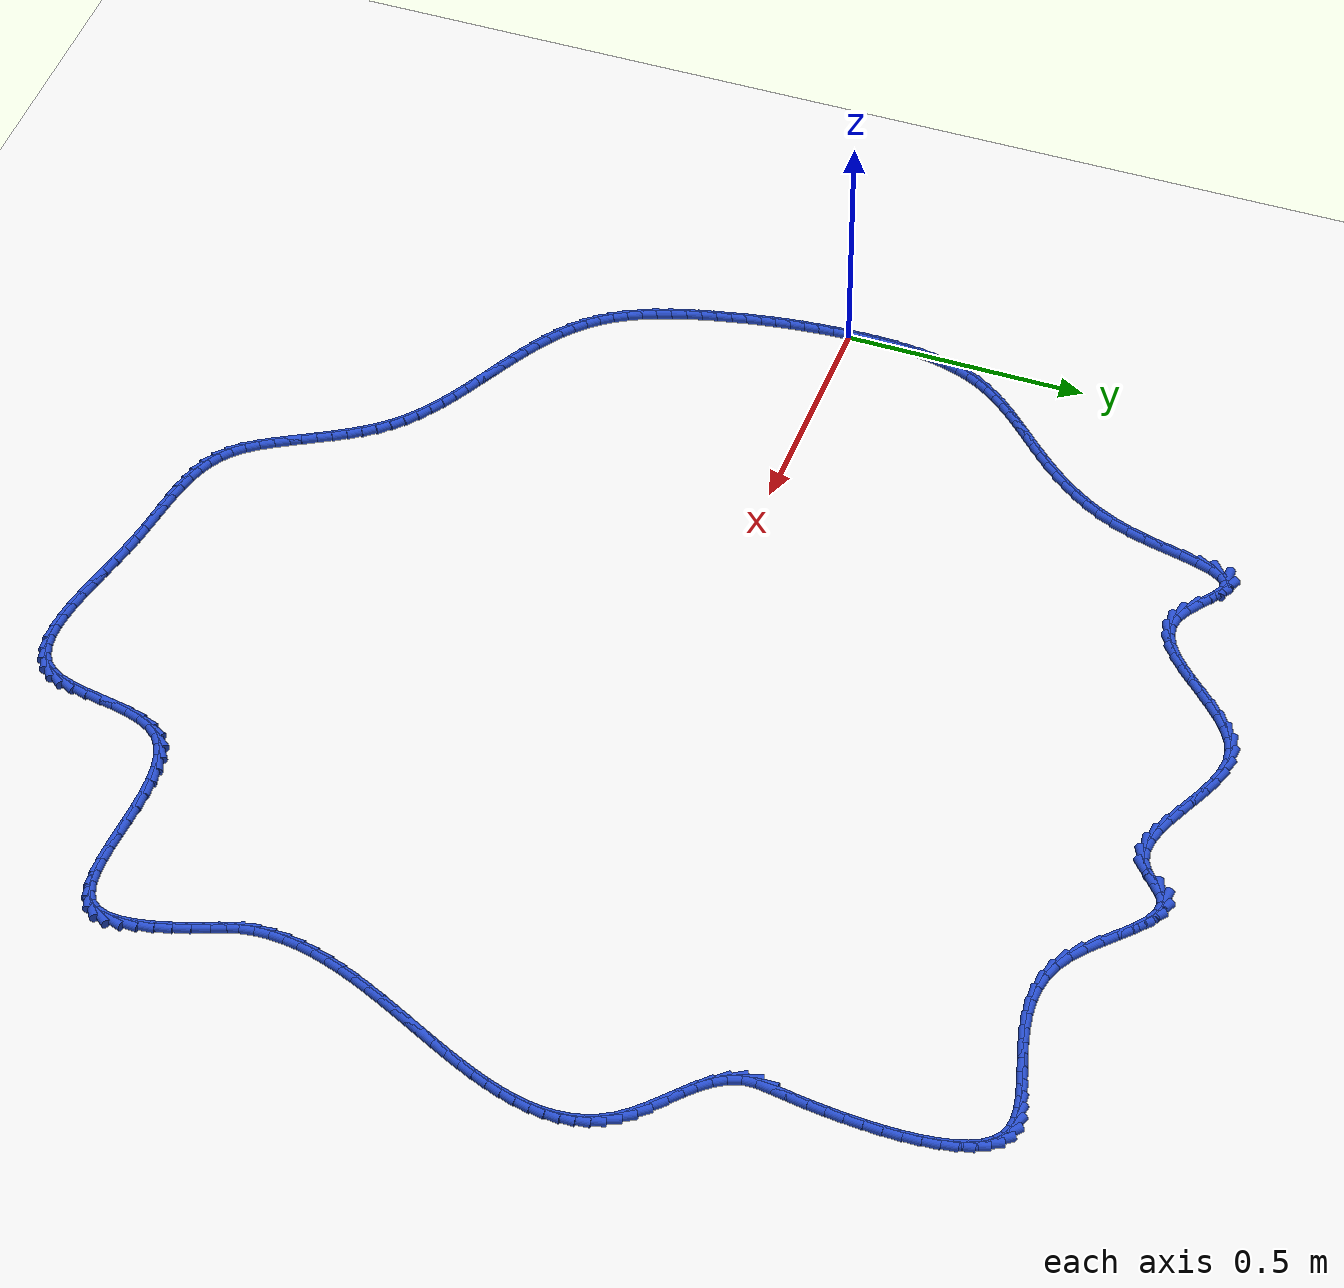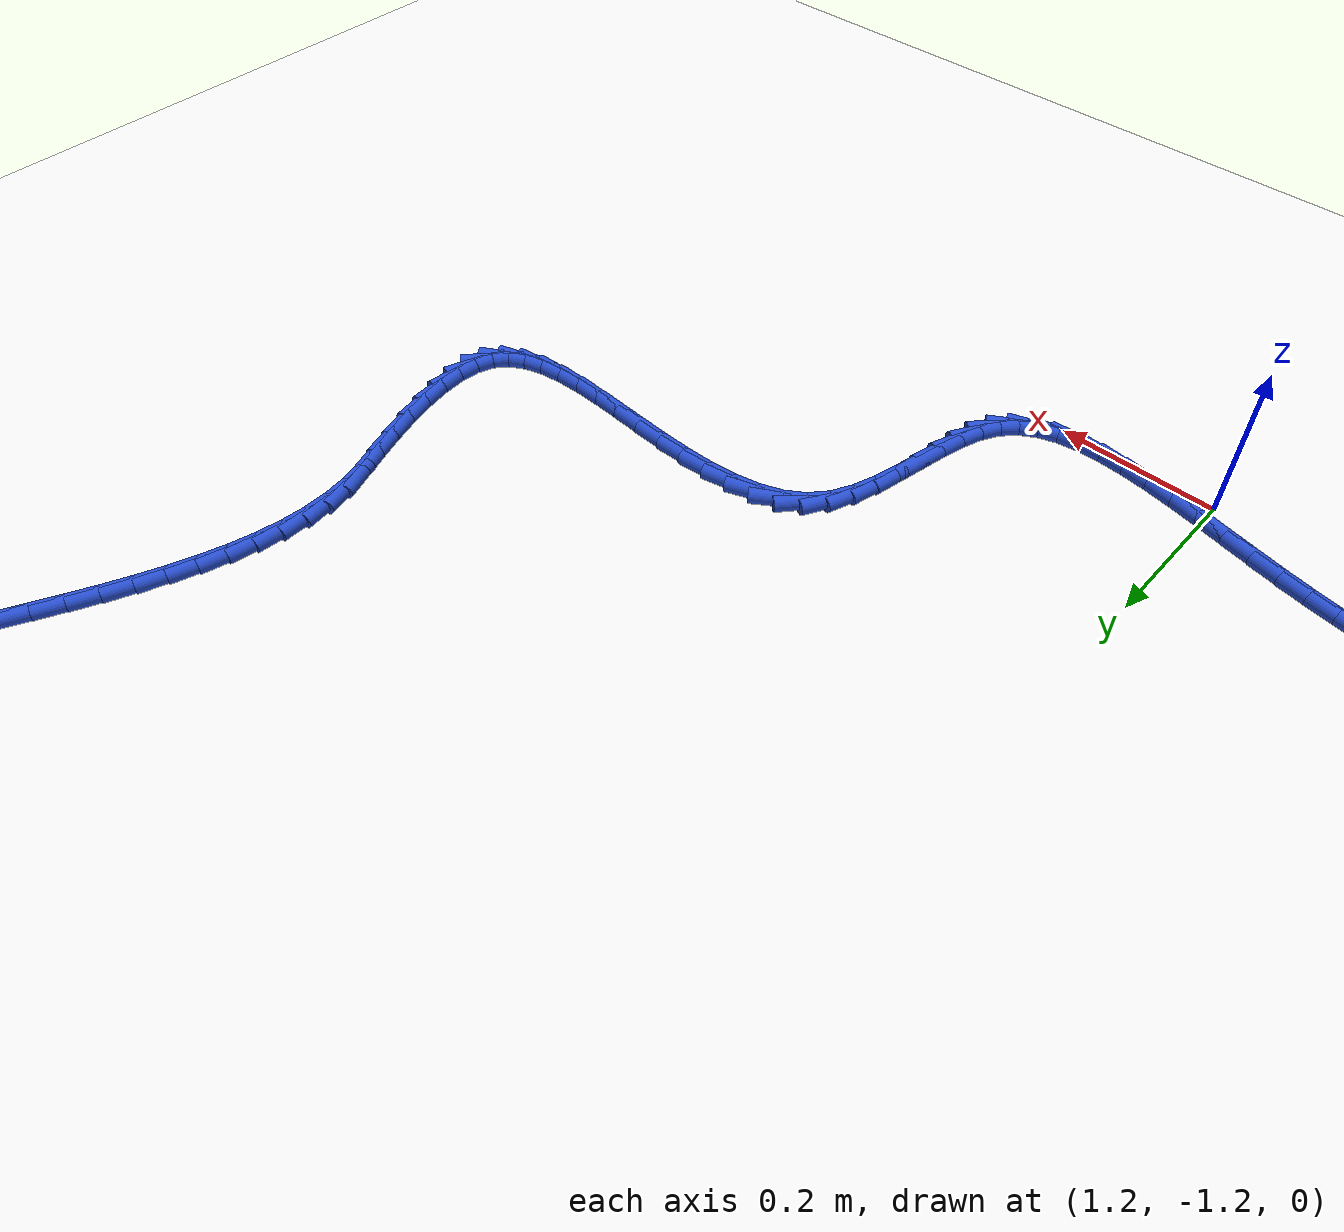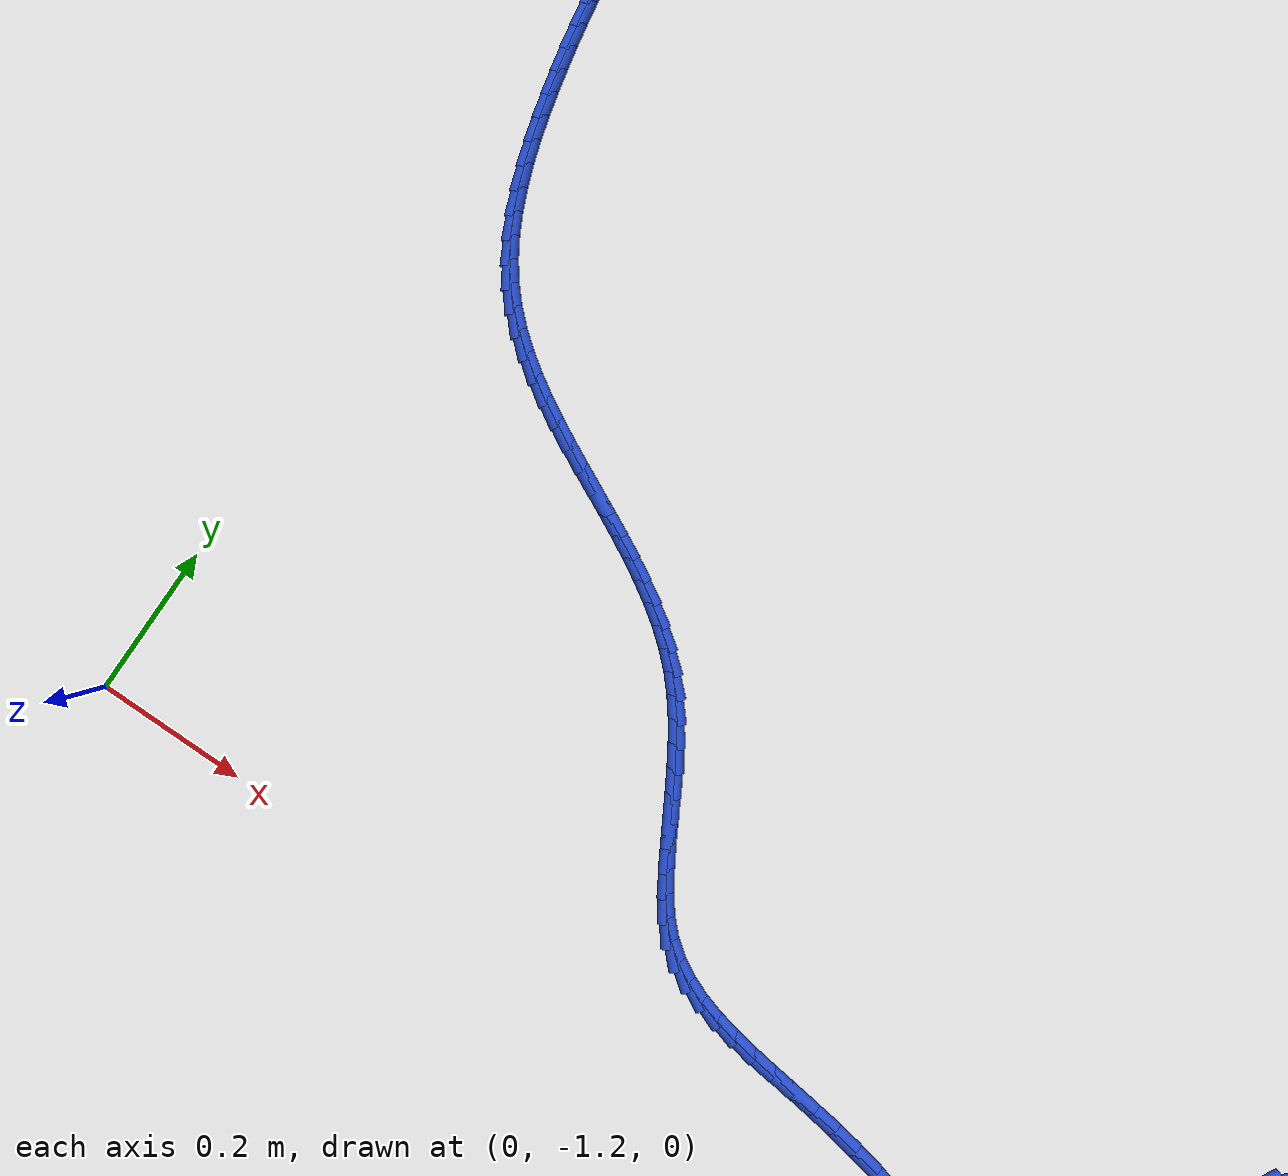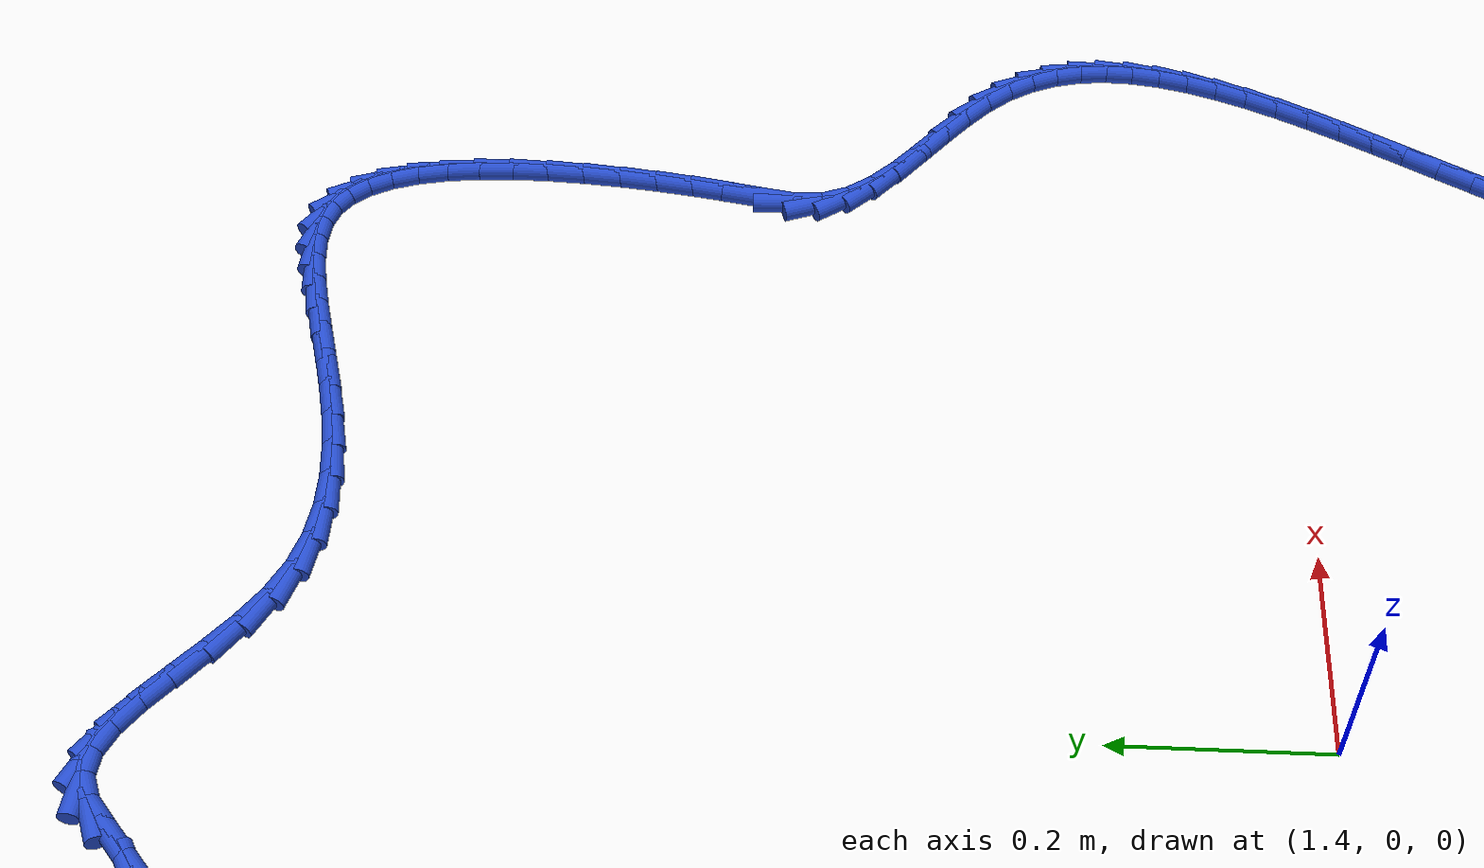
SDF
<sdf version="1.6">
 <world name="default">
  <light name="sun" type="directional">
   <pose>0 0 10 0 -0 0</pose>
   <diffuse>0.8 0.8 0.8 1</diffuse>
   <specular>0.2 0.2 0.2 1</specular>
   <attenuation>
    <range>1000</range>
    <constant>0.9</constant>
    <linear>0.01</linear>
    <quadratic>0.001</quadratic>
   </attenuation>
   <direction>-0.5 0.1 -0.9</direction>
  </light>
  <model name="ground_plane">
   <static>1</static>
   <link name="link">
    <collision name="collision">
     <geometry><plane><normal>0 0 1</normal><size>100 100</size></plane></geometry>
     <surface><friction><ode><mu>100</mu><mu2>50</mu2></ode></friction></surface>
    </collision>
    <visual name="visual">
     <cast_shadows>0</cast_shadows>
     <geometry><plane><normal>0 0 1</normal><size>100 100</size></plane></geometry>
     <material>
      <script><uri>file://media/materials/scripts/gazebo.material</uri><name>Gazebo/WhiteGlow</name></script>
     </material>
    </visual>
   </link>
  </model>
  <gravity>0 0 -9.8</gravity>
  <magnetic_field>6e-06 2.3e-05 -4.2e-05</magnetic_field>
  <atmosphere type="adiabatic"/>
  <physics name="default_physics" default="0" type="ode">
   <max_step_size>0.001</max_step_size>
   <real_time_factor>1</real_time_factor>
   <real_time_update_rate>1000</real_time_update_rate>
  </physics>
  <scene><ambient>0.4 0.4 0.4 1</ambient><background>0.7 0.7 0.7 1</background><shadows>1</shadows></scene>
  <spherical_coordinates>
   <surface_model>EARTH_WGS84</surface_model>
   <latitude_deg>0</latitude_deg>
   <longitude_deg>0</longitude_deg>
   <elevation>0</elevation>
   <heading_deg>0</heading_deg>
  </spherical_coordinates>
  <model name="line">
   <link name="link_0">
    <pose>7.37257477290143e-18 6.245004513516506e-17 0.01 0 1.57 -1.5494133009734417</pose>
    <collision name="collision">
     <geometry><cylinder><radius>0.01</radius><length>0.08</length></cylinder></geometry>
    </collision>
    <visual name="visual">
     <material>
      <script><name>Gazebo/Blue</name><uri>file://media/materials/scripts/gazebo.material</uri></script>
     </material>
     <geometry><cylinder><radius>0.01</radius><length>0.08</length></cylinder></geometry>
    </visual>
   </link>
   <link name="link_1">
    <pose>-0.0006749325290999921 0.0315591284544479 0.01 0 1.57 1.564344567423251</pose>
    <collision name="collision">
     <geometry><cylinder><radius>0.01</radius><length>0.08</length></cylinder></geometry>
    </collision>
    <visual name="visual">
     <material>
      <script><name>Gazebo/Blue</name><uri>file://media/materials/scripts/gazebo.material</uri></script>
     </material>
     <geometry><cylinder><radius>0.01</radius><length>0.08</length></cylinder></geometry>
    </visual>
   </link>
   <link name="link_2">
    <pose>-0.0004697844371241242 0.06335591964076627 0.01 0 1.57 1.531487045295233</pose>
    <collision name="collision">
     <geometry><cylinder><radius>0.01</radius><length>0.08</length></cylinder></geometry>
    </collision>
    <visual name="visual">
     <material>
      <script><name>Gazebo/Blue</name><uri>file://media/materials/scripts/gazebo.material</uri></script>
     </material>
     <geometry><cylinder><radius>0.01</radius><length>0.08</length></cylinder></geometry>
    </visual>
   </link>
   <link name="link_3">
    <pose>0.0007798856668244447 0.09513025685569365 0.01 0 1.57 1.4928821093926001</pose>
    <collision name="collision">
     <geometry><cylinder><radius>0.01</radius><length>0.08</length></cylinder></geometry>
    </collision>
    <visual name="visual">
     <material>
      <script><name>Gazebo/Blue</name><uri>file://media/materials/scripts/gazebo.material</uri></script>
     </material>
     <geometry><cylinder><radius>0.01</radius><length>0.08</length></cylinder></geometry>
    </visual>
   </link>
   <link name="link_4">
    <pose>0.0032385191736425487 0.12662202339596848 0.01 0 1.57 1.4476057868877434</pose>
    <collision name="collision">
     <geometry><cylinder><radius>0.01</radius><length>0.08</length></cylinder></geometry>
    </collision>
    <visual name="visual">
     <material>
      <script><name>Gazebo/Blue</name><uri>file://media/materials/scripts/gazebo.material</uri></script>
     </material>
     <geometry><cylinder><radius>0.01</radius><length>0.08</length></cylinder></geometry>
    </visual>
   </link>
   <link name="link_5">
    <pose>0.00707055747422702 0.15757110255832912 0.01 0 1.57 1.3945175894375843</pose>
    <collision name="collision">
     <geometry><cylinder><radius>0.01</radius><length>0.08</length></cylinder></geometry>
    </collision>
    <visual name="visual">
     <material>
      <script><name>Gazebo/Blue</name><uri>file://media/materials/scripts/gazebo.material</uri></script>
     </material>
     <geometry><cylinder><radius>0.01</radius><length>0.08</length></cylinder></geometry>
    </visual>
   </link>
   <link name="link_6">
    <pose>0.012440441959474698 0.1877173776395142 0.01 0 1.57 1.33225704031677</pose>
    <collision name="collision">
     <geometry><cylinder><radius>0.01</radius><length>0.08</length></cylinder></geometry>
    </collision>
    <visual name="visual">
     <material>
      <script><name>Gazebo/Blue</name><uri>file://media/materials/scripts/gazebo.material</uri></script>
     </material>
     <geometry><cylinder><radius>0.01</radius><length>0.08</length></cylinder></geometry>
    </visual>
   </link>
   <link name="link_7">
    <pose>0.019512614020282402 0.21680073193626206 0.01 0 1.57 1.2592776344415744</pose>
    <collision name="collision">
     <geometry><cylinder><radius>0.01</radius><length>0.08</length></cylinder></geometry>
    </collision>
    <visual name="visual">
     <material>
      <script><name>Gazebo/Blue</name><uri>file://media/materials/scripts/gazebo.material</uri></script>
     </material>
     <geometry><cylinder><radius>0.01</radius><length>0.08</length></cylinder></geometry>
    </visual>
   </link>
   <link name="link_8">
    <pose>0.028451515047546967 0.2445610487453111 0.01 0 1.57 1.1742802259034448</pose>
    <collision name="collision">
     <geometry><cylinder><radius>0.01</radius><length>0.08</length></cylinder></geometry>
    </collision>
    <visual name="visual">
     <material>
      <script><name>Gazebo/Blue</name><uri>file://media/materials/scripts/gazebo.material</uri></script>
     </material>
     <geometry><cylinder><radius>0.01</radius><length>0.08</length></cylinder></geometry>
    </visual>
   </link>
   <link name="link_9">
    <pose>0.03941522935704486 0.2707466435802484 0.01 0 1.57 1.0853854781770802</pose>
    <collision name="collision">
     <geometry><cylinder><radius>0.01</radius><length>0.08</length></cylinder></geometry>
    </collision>
    <visual name="visual">
     <material>
      <script><name>Gazebo/Blue</name><uri>file://media/materials/scripts/gazebo.material</uri></script>
     </material>
     <geometry><cylinder><radius>0.01</radius><length>0.08</length></cylinder></geometry>
    </visual>
   </link>
   <link name="link_10">
    <pose>0.05238713303723986 0.29533757023524504 0.01 0 1.57 1.004441467432523</pose>
    <collision name="collision">
     <geometry><cylinder><radius>0.01</radius><length>0.08</length></cylinder></geometry>
    </collision>
    <visual name="visual">
     <material>
      <script><name>Gazebo/Blue</name><uri>file://media/materials/scripts/gazebo.material</uri></script>
     </material>
     <geometry><cylinder><radius>0.01</radius><length>0.08</length></cylinder></geometry>
    </visual>
   </link>
   <link name="link_11">
    <pose>0.06715842345208758 0.3185687941813127 0.01 0 1.57 0.9342071787430403</pose>
    <collision name="collision">
     <geometry><cylinder><radius>0.01</radius><length>0.08</length></cylinder></geometry>
    </collision>
    <visual name="visual">
     <material>
      <script><name>Gazebo/Blue</name><uri>file://media/materials/scripts/gazebo.material</uri></script>
     </material>
     <geometry><cylinder><radius>0.01</radius><length>0.08</length></cylinder></geometry>
    </visual>
   </link>
   <link name="link_12">
    <pose>0.0835104368383181 0.34068836098708194 0.01 0 1.57 0.8760364899125974</pose>
    <collision name="collision">
     <geometry><cylinder><radius>0.01</radius><length>0.08</length></cylinder></geometry>
    </collision>
    <visual name="visual">
     <material>
      <script><name>Gazebo/Blue</name><uri>file://media/materials/scripts/gazebo.material</uri></script>
     </material>
     <geometry><cylinder><radius>0.01</radius><length>0.08</length></cylinder></geometry>
    </visual>
   </link>
   <link name="link_13">
    <pose>0.10122450943266136 0.36194431622118245 0.01 0 1.57 0.830507236091904</pose>
    <collision name="collision">
     <geometry><cylinder><radius>0.01</radius><length>0.08</length></cylinder></geometry>
    </collision>
    <visual name="visual">
     <material>
      <script><name>Gazebo/Blue</name><uri>file://media/materials/scripts/gazebo.material</uri></script>
     </material>
     <geometry><cylinder><radius>0.01</radius><length>0.08</length></cylinder></geometry>
    </visual>
   </link>
   <link name="link_14">
    <pose>0.1200819774718474 0.3825847054522442 0.01 0 1.57 0.7976474130714631</pose>
    <collision name="collision">
     <geometry><cylinder><radius>0.01</radius><length>0.08</length></cylinder></geometry>
    </collision>
    <visual name="visual">
     <material>
      <script><name>Gazebo/Blue</name><uri>file://media/materials/scripts/gazebo.material</uri></script>
     </material>
     <geometry><cylinder><radius>0.01</radius><length>0.08</length></cylinder></geometry>
    </visual>
   </link>
   <link name="link_15">
    <pose>0.13986417719260627 0.4028575742488976 0.01 0 1.57 0.7771586840766096</pose>
    <collision name="collision">
     <geometry><cylinder><radius>0.01</radius><length>0.08</length></cylinder></geometry>
    </collision>
    <visual name="visual">
     <material>
      <script><name>Gazebo/Blue</name><uri>file://media/materials/scripts/gazebo.material</uri></script>
     </material>
     <geometry><cylinder><radius>0.01</radius><length>0.08</length></cylinder></geometry>
    </visual>
   </link>
   <link name="link_16">
    <pose>0.160352444831668 0.42301096817977246 0.01 0 1.57 0.7685857170605752</pose>
    <collision name="collision">
     <geometry><cylinder><radius>0.01</radius><length>0.08</length></cylinder></geometry>
    </collision>
    <visual name="visual">
     <material>
      <script><name>Gazebo/Blue</name><uri>file://media/materials/scripts/gazebo.material</uri></script>
     </material>
     <geometry><cylinder><radius>0.01</radius><length>0.08</length></cylinder></geometry>
    </visual>
   </link>
   <link name="link_17">
    <pose>0.18132811662576256 0.44329293281349885 0.01 0 1.57 0.7714184193910074</pose>
    <collision name="collision">
     <geometry><cylinder><radius>0.01</radius><length>0.08</length></cylinder></geometry>
    </collision>
    <visual name="visual">
     <material>
      <script><name>Gazebo/Blue</name><uri>file://media/materials/scripts/gazebo.material</uri></script>
     </material>
     <geometry><cylinder><radius>0.01</radius><length>0.08</length></cylinder></geometry>
    </visual>
   </link>
   <link name="link_18">
    <pose>0.20257252881162002 0.46395151371870674 0.01 0 1.57 0.7851340331031088</pose>
    <collision name="collision">
     <geometry><cylinder><radius>0.01</radius><length>0.08</length></cylinder></geometry>
    </collision>
    <visual name="visual">
     <material>
      <script><name>Gazebo/Blue</name><uri>file://media/materials/scripts/gazebo.material</uri></script>
     </material>
     <geometry><cylinder><radius>0.01</radius><length>0.08</length></cylinder></geometry>
    </visual>
   </link>
   <link name="link_19">
    <pose>0.2238670176259704 0.4852347564640264 0.01 0 1.57 0.8091922949452807</pose>
    <collision name="collision">
     <geometry><cylinder><radius>0.01</radius><length>0.08</length></cylinder></geometry>
    </collision>
    <visual name="visual">
     <material>
      <script><name>Gazebo/Blue</name><uri>file://media/materials/scripts/gazebo.material</uri></script>
     </material>
     <geometry><cylinder><radius>0.01</radius><length>0.08</length></cylinder></geometry>
    </visual>
   </link>
   <link name="link_20">
    <pose>0.24499291930554368 0.5073907066180876 0.01 0 1.57 0.842997267074457</pose>
    <collision name="collision">
     <geometry><cylinder><radius>0.01</radius><length>0.08</length></cylinder></geometry>
    </collision>
    <visual name="visual">
     <material>
      <script><name>Gazebo/Blue</name><uri>file://media/materials/scripts/gazebo.material</uri></script>
     </material>
     <geometry><cylinder><radius>0.01</radius><length>0.08</length></cylinder></geometry>
    </visual>
   </link>
   <link name="link_21">
    <pose>0.2657315700870698 0.5306674097495204 0.01 0 1.57 0.8858393594590942</pose>
    <collision name="collision">
     <geometry><cylinder><radius>0.01</radius><length>0.08</length></cylinder></geometry>
    </collision>
    <visual name="visual">
     <material>
      <script><name>Gazebo/Blue</name><uri>file://media/materials/scripts/gazebo.material</uri></script>
     </material>
     <geometry><cylinder><radius>0.01</radius><length>0.08</length></cylinder></geometry>
    </visual>
   </link>
   <link name="link_22">
    <pose>0.2858643062072791 0.5553129114269553 0.01 0 1.57 0.9368326953475702</pose>
    <collision name="collision">
     <geometry><cylinder><radius>0.01</radius><length>0.08</length></cylinder></geometry>
    </collision>
    <visual name="visual">
     <material>
      <script><name>Gazebo/Blue</name><uri>file://media/materials/scripts/gazebo.material</uri></script>
     </material>
     <geometry><cylinder><radius>0.01</radius><length>0.08</length></cylinder></geometry>
    </visual>
   </link>
   <link name="link_23">
    <pose>0.3051724639029012 0.5815752572190216 0.01 0 1.57 0.9948658012850853</pose>
    <collision name="collision">
     <geometry><cylinder><radius>0.01</radius><length>0.08</length></cylinder></geometry>
    </collision>
    <visual name="visual">
     <material>
      <script><name>Gazebo/Blue</name><uri>file://media/materials/scripts/gazebo.material</uri></script>
     </material>
     <geometry><cylinder><radius>0.01</radius><length>0.08</length></cylinder></geometry>
    </visual>
   </link>
   <link name="link_24">
    <pose>0.3234373794106663 0.6097024926943497 0.01 0 1.57 1.0585848991596454</pose>
    <collision name="collision">
     <geometry><cylinder><radius>0.01</radius><length>0.08</length></cylinder></geometry>
    </collision>
    <visual name="visual">
     <material>
      <script><name>Gazebo/Blue</name><uri>file://media/materials/scripts/gazebo.material</uri></script>
     </material>
     <geometry><cylinder><radius>0.01</radius><length>0.08</length></cylinder></geometry>
    </visual>
   </link>
   <link name="link_25">
    <pose>0.34044038896730466 0.6399426634215701 0.01 0 1.57 1.1264250764798944</pose>
    <collision name="collision">
     <geometry><cylinder><radius>0.01</radius><length>0.08</length></cylinder></geometry>
    </collision>
    <visual name="visual">
     <material>
      <script><name>Gazebo/Blue</name><uri>file://media/materials/scripts/gazebo.material</uri></script>
     </material>
     <geometry><cylinder><radius>0.01</radius><length>0.08</length></cylinder></geometry>
    </visual>
   </link>
   <link name="link_26">
    <pose>0.35596282880954566 0.6725438149693118 0.01 0 1.57 1.196693108730085</pose>
    <collision name="collision">
     <geometry><cylinder><radius>0.01</radius><length>0.08</length></cylinder></geometry>
    </collision>
    <visual name="visual">
     <material>
      <script><name>Gazebo/Blue</name><uri>file://media/materials/scripts/gazebo.material</uri></script>
     </material>
     <geometry><cylinder><radius>0.01</radius><length>0.08</length></cylinder></geometry>
    </visual>
   </link>
   <link name="link_27">
    <pose>0.3697860351741201 0.7077539929062062 0.01 0 1.57 1.267136287806405</pose>
    <collision name="collision">
     <geometry><cylinder><radius>0.01</radius><length>0.08</length></cylinder></geometry>
    </collision>
    <visual name="visual">
     <material>
      <script><name>Gazebo/Blue</name><uri>file://media/materials/scripts/gazebo.material</uri></script>
     </material>
     <geometry><cylinder><radius>0.01</radius><length>0.08</length></cylinder></geometry>
    </visual>
   </link>
   <link name="link_28">
    <pose>0.3817046172806538 0.7457898669579235 0.01 0 1.57 1.3185308434865046</pose>
    <collision name="collision">
     <geometry><cylinder><radius>0.01</radius><length>0.08</length></cylinder></geometry>
    </collision>
    <visual name="visual">
     <material>
      <script><name>Gazebo/Blue</name><uri>file://media/materials/scripts/gazebo.material</uri></script>
     </material>
     <geometry><cylinder><radius>0.01</radius><length>0.08</length></cylinder></geometry>
    </visual>
   </link>
   <link name="link_29">
    <pose>0.39199762678412375 0.7857229392647994 0.01 0 1.57 1.3331264960094555</pose>
    <collision name="collision">
     <geometry><cylinder><radius>0.01</radius><length>0.08</length></cylinder></geometry>
    </collision>
    <visual name="visual">
     <material>
      <script><name>Gazebo/Blue</name><uri>file://media/materials/scripts/gazebo.material</uri></script>
     </material>
     <geometry><cylinder><radius>0.01</radius><length>0.08</length></cylinder></geometry>
    </visual>
   </link>
   <link name="link_30">
    <pose>0.4015557589306263 0.8251788551156206 0.01 0 1.57 1.3097695104657772</pose>
    <collision name="collision">
     <geometry><cylinder><radius>0.01</radius><length>0.08</length></cylinder></geometry>
    </collision>
    <visual name="visual">
     <material>
      <script><name>Gazebo/Blue</name><uri>file://media/materials/scripts/gazebo.material</uri></script>
     </material>
     <geometry><cylinder><radius>0.01</radius><length>0.08</length></cylinder></geometry>
    </visual>
   </link>
   <link name="link_31">
    <pose>0.4113088564795699 0.8616907194682312 0.01 0 1.57 1.234333936768814</pose>
    <collision name="collision">
     <geometry><cylinder><radius>0.01</radius><length>0.08</length></cylinder></geometry>
    </collision>
    <visual name="visual">
     <material>
      <script><name>Gazebo/Blue</name><uri>file://media/materials/scripts/gazebo.material</uri></script>
     </material>
     <geometry><cylinder><radius>0.01</radius><length>0.08</length></cylinder></geometry>
    </visual>
   </link>
   <link name="link_32">
    <pose>0.4221867621903627 0.8927916372804742 0.01 0 1.57 1.0626833598432595</pose>
    <collision name="collision">
     <geometry><cylinder><radius>0.01</radius><length>0.08</length></cylinder></geometry>
    </collision>
    <visual name="visual">
     <material>
      <script><name>Gazebo/Blue</name><uri>file://media/materials/scripts/gazebo.material</uri></script>
     </material>
     <geometry><cylinder><radius>0.01</radius><length>0.08</length></cylinder></geometry>
    </visual>
   </link>
   <link name="link_33">
    <pose>0.4351193188224129 0.9160147135101931 0.01 0 1.57 0.6802596081311569</pose>
    <collision name="collision">
     <geometry><cylinder><radius>0.01</radius><length>0.08</length></cylinder></geometry>
    </collision>
    <visual name="visual">
     <material>
      <script><name>Gazebo/Blue</name><uri>file://media/materials/scripts/gazebo.material</uri></script>
     </material>
     <geometry><cylinder><radius>0.01</radius><length>0.08</length></cylinder></geometry>
    </visual>
   </link>
   <link name="link_34">
    <pose>0.45103636913512857 0.9288930531152311 0.01 0 1.57 0.004475759901420822</pose>
    <collision name="collision">
     <geometry><cylinder><radius>0.01</radius><length>0.08</length></cylinder></geometry>
    </collision>
    <visual name="visual">
     <material>
      <script><name>Gazebo/Blue</name><uri>file://media/materials/scripts/gazebo.material</uri></script>
     </material>
     <geometry><cylinder><radius>0.01</radius><length>0.08</length></cylinder></geometry>
    </visual>
   </link>
   <link name="link_35">
    <pose>0.4708619097663652 0.9289817880675386 0.01 0 1.57 -0.47667261718434</pose>
    <collision name="collision">
     <geometry><cylinder><radius>0.01</radius><length>0.08</length></cylinder></geometry>
    </collision>
    <visual name="visual">
     <material>
      <script><name>Gazebo/Blue</name><uri>file://media/materials/scripts/gazebo.material</uri></script>
     </material>
     <geometry><cylinder><radius>0.01</radius><length>0.08</length></cylinder></geometry>
    </visual>
   </link>
   <link name="link_36">
    <pose>0.49477791926546966 0.9166318257528752 0.01 0 1.57 -0.6163897120340548</pose>
    <collision name="collision">
     <geometry><cylinder><radius>0.01</radius><length>0.08</length></cylinder></geometry>
    </collision>
    <visual name="visual">
     <material>
      <script><name>Gazebo/Blue</name><uri>file://media/materials/scripts/gazebo.material</uri></script>
     </material>
     <geometry><cylinder><radius>0.01</radius><length>0.08</length></cylinder></geometry>
    </visual>
   </link>
   <link name="link_37">
    <pose>0.5215062507462142 0.8976955335039689 0.01 0 1.57 -0.5953598450333591</pose>
    <collision name="collision">
     <geometry><cylinder><radius>0.01</radius><length>0.08</length></cylinder></geometry>
    </collision>
    <visual name="visual">
     <material>
      <script><name>Gazebo/Blue</name><uri>file://media/materials/scripts/gazebo.material</uri></script>
     </material>
     <geometry><cylinder><radius>0.01</radius><length>0.08</length></cylinder></geometry>
    </visual>
   </link>
   <link name="link_38">
    <pose>0.5495983134943707 0.8786674768305704 0.01 0 1.57 -0.4259680809941621</pose>
    <collision name="collision">
     <geometry><cylinder><radius>0.01</radius><length>0.08</length></cylinder></geometry>
    </collision>
    <visual name="visual">
     <material>
      <script><name>Gazebo/Blue</name><uri>file://media/materials/scripts/gazebo.material</uri></script>
     </material>
     <geometry><cylinder><radius>0.01</radius><length>0.08</length></cylinder></geometry>
    </visual>
   </link>
   <link name="link_39">
    <pose>0.5776242139775235 0.865950723406403 0.01 0 1.57 -0.12190410586019118</pose>
    <collision name="collision">
     <geometry><cylinder><radius>0.01</radius><length>0.08</length></cylinder></geometry>
    </collision>
    <visual name="visual">
     <material>
      <script><name>Gazebo/Blue</name><uri>file://media/materials/scripts/gazebo.material</uri></script>
     </material>
     <geometry><cylinder><radius>0.01</radius><length>0.08</length></cylinder></geometry>
    </visual>
   </link>
   <link name="link_40">
    <pose>0.6048347802592525 0.8626171141139822 0.01 0 1.57 0.1835484129497003</pose>
    <collision name="collision">
     <geometry><cylinder><radius>0.01</radius><length>0.08</length></cylinder></geometry>
    </collision>
    <visual name="visual">
     <material>
      <script><name>Gazebo/Blue</name><uri>file://media/materials/scripts/gazebo.material</uri></script>
     </material>
     <geometry><cylinder><radius>0.01</radius><length>0.08</length></cylinder></geometry>
    </visual>
   </link>
   <link name="link_41">
    <pose>0.6313393229254487 0.8675373597483966 0.01 0 1.57 0.425834711415626</pose>
    <collision name="collision">
     <geometry><cylinder><radius>0.01</radius><length>0.08</length></cylinder></geometry>
    </collision>
    <visual name="visual">
     <material>
      <script><name>Gazebo/Blue</name><uri>file://media/materials/scripts/gazebo.material</uri></script>
     </material>
     <geometry><cylinder><radius>0.01</radius><length>0.08</length></cylinder></geometry>
    </visual>
   </link>
   <link name="link_42">
    <pose>0.657302002931045 0.8793137515042155 0.01 0 1.57 0.5928084336766334</pose>
    <collision name="collision">
     <geometry><cylinder><radius>0.01</radius><length>0.08</length></cylinder></geometry>
    </collision>
    <visual name="visual">
     <material>
      <script><name>Gazebo/Blue</name><uri>file://media/materials/scripts/gazebo.material</uri></script>
     </material>
     <geometry><cylinder><radius>0.01</radius><length>0.08</length></cylinder></geometry>
    </visual>
   </link>
   <link name="link_43">
    <pose>0.6828869812309747 0.896548580576009 0.01 0 1.57 0.6982795642031482</pose>
    <collision name="collision">
     <geometry><cylinder><radius>0.01</radius><length>0.08</length></cylinder></geometry>
    </collision>
    <visual name="visual">
     <material>
      <script><name>Gazebo/Blue</name><uri>file://media/materials/scripts/gazebo.material</uri></script>
     </material>
     <geometry><cylinder><radius>0.01</radius><length>0.08</length></cylinder></geometry>
    </visual>
   </link>
   <link name="link_44">
    <pose>0.7082584187801705 0.9178441381583459 0.01 0 1.57 0.7577375476258514</pose>
    <collision name="collision">
     <geometry><cylinder><radius>0.01</radius><length>0.08</length></cylinder></geometry>
    </collision>
    <visual name="visual">
     <material>
      <script><name>Gazebo/Blue</name><uri>file://media/materials/scripts/gazebo.material</uri></script>
     </material>
     <geometry><cylinder><radius>0.01</radius><length>0.08</length></cylinder></geometry>
    </visual>
   </link>
   <link name="link_45">
    <pose>0.7335804765335658 0.9418027154457969 0.01 0 1.57 0.781194720545762</pose>
    <collision name="collision">
     <geometry><cylinder><radius>0.01</radius><length>0.08</length></cylinder></geometry>
    </collision>
    <visual name="visual">
     <material>
      <script><name>Gazebo/Blue</name><uri>file://media/materials/scripts/gazebo.material</uri></script>
     </material>
     <geometry><cylinder><radius>0.01</radius><length>0.08</length></cylinder></geometry>
    </visual>
   </link>
   <link name="link_46">
    <pose>0.7590173154460937 0.967026603632931 0.01 0 1.57 0.7731113526060213</pose>
    <collision name="collision">
     <geometry><cylinder><radius>0.01</radius><length>0.08</length></cylinder></geometry>
    </collision>
    <visual name="visual">
     <material>
      <script><name>Gazebo/Blue</name><uri>file://media/materials/scripts/gazebo.material</uri></script>
     </material>
     <geometry><cylinder><radius>0.01</radius><length>0.08</length></cylinder></geometry>
    </visual>
   </link>
   <link name="link_47">
    <pose>0.7847330964726874 0.9921180939143182 0.01 0 1.57 0.7332033256073862</pose>
    <collision name="collision">
     <geometry><cylinder><radius>0.01</radius><length>0.08</length></cylinder></geometry>
    </collision>
    <visual name="visual">
     <material>
      <script><name>Gazebo/Blue</name><uri>file://media/materials/scripts/gazebo.material</uri></script>
     </material>
     <geometry><cylinder><radius>0.01</radius><length>0.08</length></cylinder></geometry>
    </visual>
   </link>
   <link name="link_48">
    <pose>0.8108919805682797 1.015679477484528 0.01 0 1.57 0.6567328043990429</pose>
    <collision name="collision">
     <geometry><cylinder><radius>0.01</radius><length>0.08</length></cylinder></geometry>
    </collision>
    <visual name="visual">
     <material>
      <script><name>Gazebo/Blue</name><uri>file://media/materials/scripts/gazebo.material</uri></script>
     </material>
     <geometry><cylinder><radius>0.01</radius><length>0.08</length></cylinder></geometry>
    </visual>
   </link>
   <link name="link_49">
    <pose>0.837658128687804 1.0363130455381302 0.01 0 1.57 0.5346723412015636</pose>
    <collision name="collision">
     <geometry><cylinder><radius>0.01</radius><length>0.08</length></cylinder></geometry>
    </collision>
    <visual name="visual">
     <material>
      <script><name>Gazebo/Blue</name><uri>file://media/materials/scripts/gazebo.material</uri></script>
     </material>
     <geometry><cylinder><radius>0.01</radius><length>0.08</length></cylinder></geometry>
    </visual>
   </link>
   <link name="link_50">
    <pose>0.8651957017861931 1.0526210892696946 0.01 0 1.57 0.35591565333533226</pose>
    <collision name="collision">
     <geometry><cylinder><radius>0.01</radius><length>0.08</length></cylinder></geometry>
    </collision>
    <visual name="visual">
     <material>
      <script><name>Gazebo/Blue</name><uri>file://media/materials/scripts/gazebo.material</uri></script>
     </material>
     <geometry><cylinder><radius>0.01</radius><length>0.08</length></cylinder></geometry>
    </visual>
   </link>
   <link name="link_51">
    <pose>0.8936688608183803 1.0632058998737905 0.01 0 1.57 0.12244499309112532</pose>
    <collision name="collision">
     <geometry><cylinder><radius>0.01</radius><length>0.08</length></cylinder></geometry>
    </collision>
    <visual name="visual">
     <material>
      <script><name>Gazebo/Blue</name><uri>file://media/materials/scripts/gazebo.material</uri></script>
     </material>
     <geometry><cylinder><radius>0.01</radius><length>0.08</length></cylinder></geometry>
    </visual>
   </link>
   <link name="link_52">
    <pose>0.9232162190874177 1.066842015967054 0.01 0 1.57 -0.09243175683574542</pose>
    <collision name="collision">
     <geometry><cylinder><radius>0.01</radius><length>0.08</length></cylinder></geometry>
    </collision>
    <visual name="visual">
     <material>
      <script><name>Gazebo/Blue</name><uri>file://media/materials/scripts/gazebo.material</uri></script>
     </material>
     <geometry><cylinder><radius>0.01</radius><length>0.08</length></cylinder></geometry>
    </visual>
   </link>
   <link name="link_53">
    <pose>0.9537227322076788 1.0640141874672229 0.01 0 1.57 -0.2457882107280763</pose>
    <collision name="collision">
     <geometry><cylinder><radius>0.01</radius><length>0.08</length></cylinder></geometry>
    </collision>
    <visual name="visual">
     <material>
      <script><name>Gazebo/Blue</name><uri>file://media/materials/scripts/gazebo.material</uri></script>
     </material>
     <geometry><cylinder><radius>0.01</radius><length>0.08</length></cylinder></geometry>
    </visual>
   </link>
   <link name="link_54">
    <pose>0.9849281784415743 1.0561859792819512 0.01 0 1.57 -0.34449792646018007</pose>
    <collision name="collision">
     <geometry><cylinder><radius>0.01</radius><length>0.08</length></cylinder></geometry>
    </collision>
    <visual name="visual">
     <material>
      <script><name>Gazebo/Blue</name><uri>file://media/materials/scripts/gazebo.material</uri></script>
     </material>
     <geometry><cylinder><radius>0.01</radius><length>0.08</length></cylinder></geometry>
    </visual>
   </link>
   <link name="link_55">
    <pose>1.0165706256846394 1.0448324879573623 0.01 0 1.57 -0.39870474145118806</pose>
    <collision name="collision">
     <geometry><cylinder><radius>0.01</radius><length>0.08</length></cylinder></geometry>
    </collision>
    <visual name="visual">
     <material>
      <script><name>Gazebo/Blue</name><uri>file://media/materials/scripts/gazebo.material</uri></script>
     </material>
     <geometry><cylinder><radius>0.01</radius><length>0.08</length></cylinder></geometry>
    </visual>
   </link>
   <link name="link_56">
    <pose>1.0483881418324101 1.0314288100395772 0.01 0 1.57 -0.4149630537967998</pose>
    <collision name="collision">
     <geometry><cylinder><radius>0.01</radius><length>0.08</length></cylinder></geometry>
    </collision>
    <visual name="visual">
     <material>
      <script><name>Gazebo/Blue</name><uri>file://media/materials/scripts/gazebo.material</uri></script>
     </material>
     <geometry><cylinder><radius>0.01</radius><length>0.08</length></cylinder></geometry>
    </visual>
   </link>
   <link name="link_57">
    <pose>1.0801187947804214 1.0174500420747188 0.01 0 1.57 -0.39487223125939164</pose>
    <collision name="collision">
     <geometry><cylinder><radius>0.01</radius><length>0.08</length></cylinder></geometry>
    </collision>
    <visual name="visual">
     <material>
      <script><name>Gazebo/Blue</name><uri>file://media/materials/scripts/gazebo.material</uri></script>
     </material>
     <geometry><cylinder><radius>0.01</radius><length>0.08</length></cylinder></geometry>
    </visual>
   </link>
   <link name="link_58">
    <pose>1.1115006524242088 1.004371280608908 0.01 0 1.57 -0.3347558724253994</pose>
    <collision name="collision">
     <geometry><cylinder><radius>0.01</radius><length>0.08</length></cylinder></geometry>
    </collision>
    <visual name="visual">
     <material>
      <script><name>Gazebo/Blue</name><uri>file://media/materials/scripts/gazebo.material</uri></script>
     </material>
     <geometry><cylinder><radius>0.01</radius><length>0.08</length></cylinder></geometry>
    </visual>
   </link>
   <link name="link_59">
    <pose>1.1422717826593072 0.9936676221882683 0.01 0 1.57 -0.22533162533398482</pose>
    <collision name="collision">
     <geometry><cylinder><radius>0.01</radius><length>0.08</length></cylinder></geometry>
    </collision>
    <visual name="visual">
     <material>
      <script><name>Gazebo/Blue</name><uri>file://media/materials/scripts/gazebo.material</uri></script>
     </material>
     <geometry><cylinder><radius>0.01</radius><length>0.08</length></cylinder></geometry>
    </visual>
   </link>
   <link name="link_60">
    <pose>1.1721702533812526 0.9868141633589208 0.01 0 1.57 -0.05307793624961049</pose>
    <collision name="collision">
     <geometry><cylinder><radius>0.01</radius><length>0.08</length></cylinder></geometry>
    </collision>
    <visual name="visual">
     <material>
      <script><name>Gazebo/Blue</name><uri>file://media/materials/scripts/gazebo.material</uri></script>
     </material>
     <geometry><cylinder><radius>0.01</radius><length>0.08</length></cylinder></geometry>
    </visual>
   </link>
   <link name="link_61">
    <pose>1.2009341324855805 0.9852860006669882 0.01 0 1.57 0.19031515986881176</pose>
    <collision name="collision">
     <geometry><cylinder><radius>0.01</radius><length>0.08</length></cylinder></geometry>
    </collision>
    <visual name="visual">
     <material>
      <script><name>Gazebo/Blue</name><uri>file://media/materials/scripts/gazebo.material</uri></script>
     </material>
     <geometry><cylinder><radius>0.01</radius><length>0.08</length></cylinder></geometry>
    </visual>
   </link>
   <link name="link_62">
    <pose>1.2283014878678251 0.990558230658592 0.01 0 1.57 0.48491114109836597</pose>
    <collision name="collision">
     <geometry><cylinder><radius>0.01</radius><length>0.08</length></cylinder></geometry>
    </collision>
    <visual name="visual">
     <material>
      <script><name>Gazebo/Blue</name><uri>file://media/materials/scripts/gazebo.material</uri></script>
     </material>
     <geometry><cylinder><radius>0.01</radius><length>0.08</length></cylinder></geometry>
    </visual>
   </link>
   <link name="link_63">
    <pose>1.25401064218709 1.0041035904554854 0.01 0 1.57 0.7115988885600627</pose>
    <collision name="collision">
     <geometry><cylinder><radius>0.01</radius><length>0.08</length></cylinder></geometry>
    </collision>
    <visual name="visual">
     <material>
      <script><name>Gazebo/Blue</name><uri>file://media/materials/scripts/gazebo.material</uri></script>
     </material>
     <geometry><cylinder><radius>0.01</radius><length>0.08</length></cylinder></geometry>
    </visual>
   </link>
   <link name="link_64">
    <pose>1.2780742719995617 1.0248539622278146 0.01 0 1.57 0.6986634431958092</pose>
    <collision name="collision">
     <geometry><cylinder><radius>0.01</radius><length>0.08</length></cylinder></geometry>
    </collision>
    <visual name="visual">
     <material>
      <script><name>Gazebo/Blue</name><uri>file://media/materials/scripts/gazebo.material</uri></script>
     </material>
     <geometry><cylinder><radius>0.01</radius><length>0.08</length></cylinder></geometry>
    </visual>
   </link>
   <link name="link_65">
    <pose>1.301301517719232 1.0443649919836653 0.01 0 1.57 0.3820760768623614</pose>
    <collision name="collision">
     <geometry><cylinder><radius>0.01</radius><length>0.08</length></cylinder></geometry>
    </collision>
    <visual name="visual">
     <material>
      <script><name>Gazebo/Blue</name><uri>file://media/materials/scripts/gazebo.material</uri></script>
     </material>
     <geometry><cylinder><radius>0.01</radius><length>0.08</length></cylinder></geometry>
    </visual>
   </link>
   <link name="link_66">
    <pose>1.324588043439721 1.0537220302565646 0.01 0 1.57 -0.0945205677847257</pose>
    <collision name="collision">
     <geometry><cylinder><radius>0.01</radius><length>0.08</length></cylinder></geometry>
    </collision>
    <visual name="visual">
     <material>
      <script><name>Gazebo/Blue</name><uri>file://media/materials/scripts/gazebo.material</uri></script>
     </material>
     <geometry><cylinder><radius>0.01</radius><length>0.08</length></cylinder></geometry>
    </visual>
   </link>
   <link name="link_67">
    <pose>1.3483337762712888 1.0514708620281081 0.01 0 1.57 -0.4407224927175288</pose>
    <collision name="collision">
     <geometry><cylinder><radius>0.01</radius><length>0.08</length></cylinder></geometry>
    </collision>
    <visual name="visual">
     <material>
      <script><name>Gazebo/Blue</name><uri>file://media/materials/scripts/gazebo.material</uri></script>
     </material>
     <geometry><cylinder><radius>0.01</radius><length>0.08</length></cylinder></geometry>
    </visual>
   </link>
   <link name="link_68">
    <pose>1.3726842533809163 1.039985631994366 0.01 0 1.57 -0.6303660260669522</pose>
    <collision name="collision">
     <geometry><cylinder><radius>0.01</radius><length>0.08</length></cylinder></geometry>
    </collision>
    <visual name="visual">
     <material>
      <script><name>Gazebo/Blue</name><uri>file://media/materials/scripts/gazebo.material</uri></script>
     </material>
     <geometry><cylinder><radius>0.01</radius><length>0.08</length></cylinder></geometry>
    </visual>
   </link>
   <link name="link_69">
    <pose>1.397782935124112 1.0216717391583878 0.01 0 1.57 -0.7187341791752794</pose>
    <collision name="collision">
     <geometry><cylinder><radius>0.01</radius><length>0.08</length></cylinder></geometry>
    </collision>
    <visual name="visual">
     <material>
      <script><name>Gazebo/Blue</name><uri>file://media/materials/scripts/gazebo.material</uri></script>
     </material>
     <geometry><cylinder><radius>0.01</radius><length>0.08</length></cylinder></geometry>
    </visual>
   </link>
   <link name="link_70">
    <pose>1.4237732818563849 0.9989345825232223 0.01 0 1.57 -0.7415786263005891</pose>
    <collision name="collision">
     <geometry><cylinder><radius>0.01</radius><length>0.08</length></cylinder></geometry>
    </collision>
    <visual name="visual">
     <material>
      <script><name>Gazebo/Blue</name><uri>file://media/materials/scripts/gazebo.material</uri></script>
     </material>
     <geometry><cylinder><radius>0.01</radius><length>0.08</length></cylinder></geometry>
    </visual>
   </link>
   <link name="link_71">
    <pose>1.4507987539332425 0.9741795610919196 0.01 0 1.57 -0.7125492239622521</pose>
    <collision name="collision">
     <geometry><cylinder><radius>0.01</radius><length>0.08</length></cylinder></geometry>
    </collision>
    <visual name="visual">
     <material>
      <script><name>Gazebo/Blue</name><uri>file://media/materials/scripts/gazebo.material</uri></script>
     </material>
     <geometry><cylinder><radius>0.01</radius><length>0.08</length></cylinder></geometry>
    </visual>
   </link>
   <link name="link_72">
    <pose>1.4790028117101937 0.9498120738675285 0.01 0 1.57 -0.6310305010271452</pose>
    <collision name="collision">
     <geometry><cylinder><radius>0.01</radius><length>0.08</length></cylinder></geometry>
    </collision>
    <visual name="visual">
     <material>
      <script><name>Gazebo/Blue</name><uri>file://media/materials/scripts/gazebo.material</uri></script>
     </material>
     <geometry><cylinder><radius>0.01</radius><length>0.08</length></cylinder></geometry>
    </visual>
   </link>
   <link name="link_73">
    <pose>1.5085289155427466 0.9282375198530987 0.01 0 1.57 -0.4873772878341161</pose>
    <collision name="collision">
     <geometry><cylinder><radius>0.01</radius><length>0.08</length></cylinder></geometry>
    </collision>
    <visual name="visual">
     <material>
      <script><name>Gazebo/Blue</name><uri>file://media/materials/scripts/gazebo.material</uri></script>
     </material>
     <geometry><cylinder><radius>0.01</radius><length>0.08</length></cylinder></geometry>
    </visual>
   </link>
   <link name="link_74">
    <pose>1.539513671873499 0.911814856487275 0.01 0 1.57 -0.30938280196421764</pose>
    <collision name="collision">
     <geometry><cylinder><radius>0.01</radius><length>0.08</length></cylinder></geometry>
    </collision>
    <visual name="visual">
     <material>
      <script><name>Gazebo/Blue</name><uri>file://media/materials/scripts/gazebo.material</uri></script>
     </material>
     <geometry><cylinder><radius>0.01</radius><length>0.08</length></cylinder></geometry>
    </visual>
   </link>
   <link name="link_75">
    <pose>1.5718819644609074 0.9014684252749491 0.01 0 1.57 -0.1490378007712887</pose>
    <collision name="collision">
     <geometry><cylinder><radius>0.01</radius><length>0.08</length></cylinder></geometry>
    </collision>
    <visual name="visual">
     <material>
      <script><name>Gazebo/Blue</name><uri>file://media/materials/scripts/gazebo.material</uri></script>
     </material>
     <geometry><cylinder><radius>0.01</radius><length>0.08</length></cylinder></geometry>
    </visual>
   </link>
   <link name="link_76">
    <pose>1.6053116768973987 0.896448914398174 0.01 0 1.57 -0.01570670925698995</pose>
    <collision name="collision">
     <geometry><cylinder><radius>0.01</radius><length>0.08</length></cylinder></geometry>
    </collision>
    <visual name="visual">
     <material>
      <script><name>Gazebo/Blue</name><uri>file://media/materials/scripts/gazebo.material</uri></script>
     </material>
     <geometry><cylinder><radius>0.01</radius><length>0.08</length></cylinder></geometry>
    </visual>
   </link>
   <link name="link_77">
    <pose>1.639466730794724 0.8959124067772882 0.01 0 1.57 0.08957410415533272</pose>
    <collision name="collision">
     <geometry><cylinder><radius>0.01</radius><length>0.08</length></cylinder></geometry>
    </collision>
    <visual name="visual">
     <material>
      <script><name>Gazebo/Blue</name><uri>file://media/materials/scripts/gazebo.material</uri></script>
     </material>
     <geometry><cylinder><radius>0.01</radius><length>0.08</length></cylinder></geometry>
    </visual>
   </link>
   <link name="link_78">
    <pose>1.6740110477646342 0.8990149853326305 0.01 0 1.57 0.16884443567637286</pose>
    <collision name="collision">
     <geometry><cylinder><radius>0.01</radius><length>0.08</length></cylinder></geometry>
    </collision>
    <visual name="visual">
     <material>
      <script><name>Gazebo/Blue</name><uri>file://media/materials/scripts/gazebo.material</uri></script>
     </material>
     <geometry><cylinder><radius>0.01</radius><length>0.08</length></cylinder></geometry>
    </visual>
   </link>
   <link name="link_79">
    <pose>1.7086085494188787 0.9049127329845392 0.01 0 1.57 0.22486793712068964</pose>
    <collision name="collision">
     <geometry><cylinder><radius>0.01</radius><length>0.08</length></cylinder></geometry>
    </collision>
    <visual name="visual">
     <material>
      <script><name>Gazebo/Blue</name><uri>file://media/materials/scripts/gazebo.material</uri></script>
     </material>
     <geometry><cylinder><radius>0.01</radius><length>0.08</length></cylinder></geometry>
    </visual>
   </link>
   <link name="link_80">
    <pose>1.7429231573692083 0.9127617326533528 0.01 0 1.57 0.2597940476123491</pose>
    <collision name="collision">
     <geometry><cylinder><radius>0.01</radius><length>0.08</length></cylinder></geometry>
    </collision>
    <visual name="visual">
     <material>
      <script><name>Gazebo/Blue</name><uri>file://media/materials/scripts/gazebo.material</uri></script>
     </material>
     <geometry><cylinder><radius>0.01</radius><length>0.08</length></cylinder></geometry>
    </visual>
   </link>
   <link name="link_81">
    <pose>1.7766187932273756 0.9217180672594103 0.01 0 1.57 0.27449186789352664</pose>
    <collision name="collision">
     <geometry><cylinder><radius>0.01</radius><length>0.08</length></cylinder></geometry>
    </collision>
    <visual name="visual">
     <material>
      <script><name>Gazebo/Blue</name><uri>file://media/materials/scripts/gazebo.material</uri></script>
     </material>
     <geometry><cylinder><radius>0.01</radius><length>0.08</length></cylinder></geometry>
    </visual>
   </link>
   <link name="link_82">
    <pose>1.809359378605129 0.9309378197230493 0.01 0 1.57 0.26808987006925306</pose>
    <collision name="collision">
     <geometry><cylinder><radius>0.01</radius><length>0.08</length></cylinder></geometry>
    </collision>
    <visual name="visual">
     <material>
      <script><name>Gazebo/Blue</name><uri>file://media/materials/scripts/gazebo.material</uri></script>
     </material>
     <geometry><cylinder><radius>0.01</radius><length>0.08</length></cylinder></geometry>
    </visual>
   </link>
   <link name="link_83">
    <pose>1.840808835114219 0.9395770729646082 0.01 0 1.57 0.23736717130398002</pose>
    <collision name="collision">
     <geometry><cylinder><radius>0.01</radius><length>0.08</length></cylinder></geometry>
    </collision>
    <visual name="visual">
     <material>
      <script><name>Gazebo/Blue</name><uri>file://media/materials/scripts/gazebo.material</uri></script>
     </material>
     <geometry><cylinder><radius>0.01</radius><length>0.08</length></cylinder></geometry>
    </visual>
   </link>
   <link name="link_84">
    <pose>1.8706310843663987 0.9467919099044267 0.01 0 1.57 0.17572384812159933</pose>
    <collision name="collision">
     <geometry><cylinder><radius>0.01</radius><length>0.08</length></cylinder></geometry>
    </collision>
    <visual name="visual">
     <material>
      <script><name>Gazebo/Blue</name><uri>file://media/materials/scripts/gazebo.material</uri></script>
     </material>
     <geometry><cylinder><radius>0.01</radius><length>0.08</length></cylinder></geometry>
    </visual>
   </link>
   <link name="link_85">
    <pose>1.898490047973417 0.9517384134628424 0.01 0 1.57 0.0716409489124832</pose>
    <collision name="collision">
     <geometry><cylinder><radius>0.01</radius><length>0.08</length></cylinder></geometry>
    </collision>
    <visual name="visual">
     <material>
      <script><name>Gazebo/Blue</name><uri>file://media/materials/scripts/gazebo.material</uri></script>
     </material>
     <geometry><cylinder><radius>0.01</radius><length>0.08</length></cylinder></geometry>
    </visual>
   </link>
   <link name="link_86">
    <pose>1.9240496475470243 0.9535726665601938 0.01 0 1.57 -0.09229937446221288</pose>
    <collision name="collision">
     <geometry><cylinder><radius>0.01</radius><length>0.08</length></cylinder></geometry>
    </collision>
    <visual name="visual">
     <material>
      <script><name>Gazebo/Blue</name><uri>file://media/materials/scripts/gazebo.material</uri></script>
     </material>
     <geometry><cylinder><radius>0.01</radius><length>0.08</length></cylinder></geometry>
    </visual>
   </link>
   <link name="link_87">
    <pose>1.9469738046989722 0.9514507521168196 0.01 0 1.57 -0.33392967617995345</pose>
    <collision name="collision">
     <geometry><cylinder><radius>0.01</radius><length>0.08</length></cylinder></geometry>
    </collision>
    <visual name="visual">
     <material>
      <script><name>Gazebo/Blue</name><uri>file://media/materials/scripts/gazebo.material</uri></script>
     </material>
     <geometry><cylinder><radius>0.01</radius><length>0.08</length></cylinder></geometry>
    </visual>
   </link>
   <link name="link_88">
    <pose>1.9669264410410099 0.944528753053058 0.01 0 1.57 -0.6359591827865287</pose>
    <collision name="collision">
     <geometry><cylinder><radius>0.01</radius><length>0.08</length></cylinder></geometry>
    </collision>
    <visual name="visual">
     <material>
      <script><name>Gazebo/Blue</name><uri>file://media/materials/scripts/gazebo.material</uri></script>
     </material>
     <geometry><cylinder><radius>0.01</radius><length>0.08</length></cylinder></geometry>
    </visual>
   </link>
   <link name="link_89">
    <pose>1.9836561385322653 0.9321775218461132 0.01 0 1.57 -0.9080077865884114</pose>
    <collision name="collision">
     <geometry><cylinder><radius>0.01</radius><length>0.08</length></cylinder></geometry>
    </collision>
    <visual name="visual">
     <material>
      <script><name>Gazebo/Blue</name><uri>file://media/materials/scripts/gazebo.material</uri></script>
     </material>
     <geometry><cylinder><radius>0.01</radius><length>0.08</length></cylinder></geometry>
    </visual>
   </link>
   <link name="link_90">
    <pose>1.9972855750331053 0.9147169315409786 0.01 0 1.57 -1.1158771694194514</pose>
    <collision name="collision">
     <geometry><cylinder><radius>0.01</radius><length>0.08</length></cylinder></geometry>
    </collision>
    <visual name="visual">
     <material>
      <script><name>Gazebo/Blue</name><uri>file://media/materials/scripts/gazebo.material</uri></script>
     </material>
     <geometry><cylinder><radius>0.01</radius><length>0.08</length></cylinder></geometry>
    </visual>
   </link>
   <link name="link_91">
    <pose>2.008040724752363 0.8927289012487554 0.01 0 1.57 -1.2678198245546224</pose>
    <collision name="collision">
     <geometry><cylinder><radius>0.01</radius><length>0.08</length></cylinder></geometry>
    </collision>
    <visual name="visual">
     <material>
      <script><name>Gazebo/Blue</name><uri>file://media/materials/scripts/gazebo.material</uri></script>
     </material>
     <geometry><cylinder><radius>0.01</radius><length>0.08</length></cylinder></geometry>
    </visual>
   </link>
   <link name="link_92">
    <pose>2.0161475653172873 0.8667953587525244 0.01 0 1.57 -1.3791480973832186</pose>
    <collision name="collision">
     <geometry><cylinder><radius>0.01</radius><length>0.08</length></cylinder></geometry>
    </collision>
    <visual name="visual">
     <material>
      <script><name>Gazebo/Blue</name><uri>file://media/materials/scripts/gazebo.material</uri></script>
     </material>
     <geometry><cylinder><radius>0.01</radius><length>0.08</length></cylinder></geometry>
    </visual>
   </link>
   <link name="link_93">
    <pose>2.0218320743551335 0.8374982318353672 0.01 0 1.57 -1.4624847339812372</pose>
    <collision name="collision">
     <geometry><cylinder><radius>0.01</radius><length>0.08</length></cylinder></geometry>
    </collision>
    <visual name="visual">
     <material>
      <script><name>Gazebo/Blue</name><uri>file://media/materials/scripts/gazebo.material</uri></script>
     </material>
     <geometry><cylinder><radius>0.01</radius><length>0.08</length></cylinder></geometry>
    </visual>
   </link>
   <link name="link_94">
    <pose>2.0253202294931527 0.8054194482803664 0.01 0 1.57 -1.526547377781316</pose>
    <collision name="collision">
     <geometry><cylinder><radius>0.01</radius><length>0.08</length></cylinder></geometry>
    </collision>
    <visual name="visual">
     <material>
      <script><name>Gazebo/Blue</name><uri>file://media/materials/scripts/gazebo.material</uri></script>
     </material>
     <geometry><cylinder><radius>0.01</radius><length>0.08</length></cylinder></geometry>
    </visual>
   </link>
   <link name="link_95">
    <pose>2.026838008358597 0.7711409358706023 0.01 0 1.57 1.56448323368767</pose>
    <collision name="collision">
     <geometry><cylinder><radius>0.01</radius><length>0.08</length></cylinder></geometry>
    </collision>
    <visual name="visual">
     <material>
      <script><name>Gazebo/Blue</name><uri>file://media/materials/scripts/gazebo.material</uri></script>
     </material>
     <geometry><cylinder><radius>0.01</radius><length>0.08</length></cylinder></geometry>
    </visual>
   </link>
   <link name="link_96">
    <pose>2.02661138857872 0.7352446223891569 0.01 0 1.57 1.5235815784366826</pose>
    <collision name="collision">
     <geometry><cylinder><radius>0.01</radius><length>0.08</length></cylinder></geometry>
    </collision>
    <visual name="visual">
     <material>
      <script><name>Gazebo/Blue</name><uri>file://media/materials/scripts/gazebo.material</uri></script>
     </material>
     <geometry><cylinder><radius>0.01</radius><length>0.08</length></cylinder></geometry>
    </visual>
   </link>
   <link name="link_97">
    <pose>2.024866347780771 0.698312435619112 0.01 0 1.57 1.489728109381425</pose>
    <collision name="collision">
     <geometry><cylinder><radius>0.01</radius><length>0.08</length></cylinder></geometry>
    </collision>
    <visual name="visual">
     <material>
      <script><name>Gazebo/Blue</name><uri>file://media/materials/scripts/gazebo.material</uri></script>
     </material>
     <geometry><cylinder><radius>0.01</radius><length>0.08</length></cylinder></geometry>
    </visual>
   </link>
   <link name="link_98">
    <pose>2.021828863592006 0.6609263033435493 0.01 0 1.57 1.461089531028589</pose>
    <collision name="collision">
     <geometry><cylinder><radius>0.01</radius><length>0.08</length></cylinder></geometry>
    </collision>
    <visual name="visual">
     <material>
      <script><name>Gazebo/Blue</name><uri>file://media/materials/scripts/gazebo.material</uri></script>
     </material>
     <geometry><cylinder><radius>0.01</radius><length>0.08</length></cylinder></geometry>
    </visual>
   </link>
   <link name="link_99">
    <pose>2.0177249136396753 0.6236681533455499 0.01 0 1.57 1.4363274567013842</pose>
    <collision name="collision">
     <geometry><cylinder><radius>0.01</radius><length>0.08</length></cylinder></geometry>
    </collision>
    <visual name="visual">
     <material>
      <script><name>Gazebo/Blue</name><uri>file://media/materials/scripts/gazebo.material</uri></script>
     </material>
     <geometry><cylinder><radius>0.01</radius><length>0.08</length></cylinder></geometry>
    </visual>
   </link>
   <link name="link_100">
    <pose>2.0127804755510317 0.587119913408195 0.01 0 1.57 1.4144117438937454</pose>
    <collision name="collision">
     <geometry><cylinder><radius>0.01</radius><length>0.08</length></cylinder></geometry>
    </collision>
    <visual name="visual">
     <material>
      <script><name>Gazebo/Blue</name><uri>file://media/materials/scripts/gazebo.material</uri></script>
     </material>
     <geometry><cylinder><radius>0.01</radius><length>0.08</length></cylinder></geometry>
    </visual>
   </link>
   <link name="link_101">
    <pose>2.0072215269533267 0.551863511314567 0.01 0 1.57 1.3944853144687042</pose>
    <collision name="collision">
     <geometry><cylinder><radius>0.01</radius><length>0.08</length></cylinder></geometry>
    </collision>
    <visual name="visual">
     <material>
      <script><name>Gazebo/Blue</name><uri>file://media/materials/scripts/gazebo.material</uri></script>
     </material>
     <geometry><cylinder><radius>0.01</radius><length>0.08</length></cylinder></geometry>
    </visual>
   </link>
   <link name="link_102">
    <pose>2.0012740454738136 0.5184808748477472 0.01 0 1.57 1.4051518582933649</pose>
    <collision name="collision">
     <geometry><cylinder><radius>0.01</radius><length>0.08</length></cylinder></geometry>
    </collision>
    <visual name="visual">
     <material>
      <script><name>Gazebo/Blue</name><uri>file://media/materials/scripts/gazebo.material</uri></script>
     </material>
     <geometry><cylinder><radius>0.01</radius><length>0.08</length></cylinder></geometry>
    </visual>
   </link>
   <link name="link_103">
    <pose>1.9960893519847014 0.4874675412518961 0.01 0 1.57 -1.5402359649732213</pose>
    <collision name="collision">
     <geometry><cylinder><radius>0.01</radius><length>0.08</length></cylinder></geometry>
    </collision>
    <visual name="visual">
     <material>
      <script><name>Gazebo/Blue</name><uri>file://media/materials/scripts/gazebo.material</uri></script>
     </material>
     <geometry><cylinder><radius>0.01</radius><length>0.08</length></cylinder></geometry>
    </visual>
   </link>
   <link name="link_104">
    <pose>1.9969624749358947 0.45890599719059944 0.01 0 1.57 -1.2296406317065611</pose>
    <collision name="collision">
     <geometry><cylinder><radius>0.01</radius><length>0.08</length></cylinder></geometry>
    </collision>
    <visual name="visual">
     <material>
      <script><name>Gazebo/Blue</name><uri>file://media/materials/scripts/gazebo.material</uri></script>
     </material>
     <geometry><cylinder><radius>0.01</radius><length>0.08</length></cylinder></geometry>
    </visual>
   </link>
   <link name="link_105">
    <pose>2.006317318165327 0.4325571255874145 0.01 0 1.57 -0.9887238100219239</pose>
    <collision name="collision">
     <geometry><cylinder><radius>0.01</radius><length>0.08</length></cylinder></geometry>
    </collision>
    <visual name="visual">
     <material>
      <script><name>Gazebo/Blue</name><uri>file://media/materials/scripts/gazebo.material</uri></script>
     </material>
     <geometry><cylinder><radius>0.01</radius><length>0.08</length></cylinder></geometry>
    </visual>
   </link>
   <link name="link_106">
    <pose>2.022491972639365 0.40798061179572853 0.01 0 1.57 -0.8325203542580724</pose>
    <collision name="collision">
     <geometry><cylinder><radius>0.01</radius><length>0.08</length></cylinder></geometry>
    </collision>
    <visual name="visual">
     <material>
      <script><name>Gazebo/Blue</name><uri>file://media/materials/scripts/gazebo.material</uri></script>
     </material>
     <geometry><cylinder><radius>0.01</radius><length>0.08</length></cylinder></geometry>
    </visual>
   </link>
   <link name="link_107">
    <pose>2.0436506749031147 0.3847275809873961 0.01 0 1.57 -0.7441118585724075</pose>
    <collision name="collision">
     <geometry><cylinder><radius>0.01</radius><length>0.08</length></cylinder></geometry>
    </collision>
    <visual name="visual">
     <material>
      <script><name>Gazebo/Blue</name><uri>file://media/materials/scripts/gazebo.material</uri></script>
     </material>
     <geometry><cylinder><radius>0.01</radius><length>0.08</length></cylinder></geometry>
    </visual>
   </link>
   <link name="link_108">
    <pose>2.067957661501684 0.36234915833427117 0.01 0 1.57 -0.7084712514834411</pose>
    <collision name="collision">
     <geometry><cylinder><radius>0.01</radius><length>0.08</length></cylinder></geometry>
    </collision>
    <visual name="visual">
     <material>
      <script><name>Gazebo/Blue</name><uri>file://media/materials/scripts/gazebo.material</uri></script>
     </material>
     <geometry><cylinder><radius>0.01</radius><length>0.08</length></cylinder></geometry>
    </visual>
   </link>
   <link name="link_109">
    <pose>2.0935771689801763 0.34039646900820864 0.01 0 1.57 -0.7192044833671358</pose>
    <collision name="collision">
     <geometry><cylinder><radius>0.01</radius><length>0.08</length></cylinder></geometry>
    </collision>
    <visual name="visual">
     <material>
      <script><name>Gazebo/Blue</name><uri>file://media/materials/scripts/gazebo.material</uri></script>
     </material>
     <geometry><cylinder><radius>0.01</radius><length>0.08</length></cylinder></geometry>
    </visual>
   </link>
   <link name="link_110">
    <pose>2.1186734338836986 0.3184206381810623 0.01 0 1.57 -0.7789932263470085</pose>
    <collision name="collision">
     <geometry><cylinder><radius>0.01</radius><length>0.08</length></cylinder></geometry>
    </collision>
    <visual name="visual">
     <material>
      <script><name>Gazebo/Blue</name><uri>file://media/materials/scripts/gazebo.material</uri></script>
     </material>
     <geometry><cylinder><radius>0.01</radius><length>0.08</length></cylinder></geometry>
    </visual>
   </link>
   <link name="link_111">
    <pose>2.141410692757358 0.2959727910246867 0.01 0 1.57 -0.8961722533705546</pose>
    <collision name="collision">
     <geometry><cylinder><radius>0.01</radius><length>0.08</length></cylinder></geometry>
    </collision>
    <visual name="visual">
     <material>
      <script><name>Gazebo/Blue</name><uri>file://media/materials/scripts/gazebo.material</uri></script>
     </material>
     <geometry><cylinder><radius>0.01</radius><length>0.08</length></cylinder></geometry>
    </visual>
   </link>
   <link name="link_112">
    <pose>2.160077550934978 0.27263362720427353 0.01 0 1.57 -1.044257659643109</pose>
    <collision name="collision">
     <geometry><cylinder><radius>0.01</radius><length>0.08</length></cylinder></geometry>
    </collision>
    <visual name="visual">
     <material>
      <script><name>Gazebo/Blue</name><uri>file://media/materials/scripts/gazebo.material</uri></script>
     </material>
     <geometry><cylinder><radius>0.01</radius><length>0.08</length></cylinder></geometry>
    </visual>
   </link>
   <link name="link_113">
    <pose>2.174230624896052 0.2482853753101304 0.01 0 1.57 -1.196534141106438</pose>
    <collision name="collision">
     <geometry><cylinder><radius>0.01</radius><length>0.08</length></cylinder></geometry>
    </collision>
    <visual name="visual">
     <material>
      <script><name>Gazebo/Blue</name><uri>file://media/materials/scripts/gazebo.material</uri></script>
     </material>
     <geometry><cylinder><radius>0.01</radius><length>0.08</length></cylinder></geometry>
    </visual>
   </link>
   <link name="link_114">
    <pose>2.1841674057869787 0.22298644151800492 0.01 0 1.57 -1.344589756408493</pose>
    <collision name="collision">
     <geometry><cylinder><radius>0.01</radius><length>0.08</length></cylinder></geometry>
    </collision>
    <visual name="visual">
     <material>
      <script><name>Gazebo/Blue</name><uri>file://media/materials/scripts/gazebo.material</uri></script>
     </material>
     <geometry><cylinder><radius>0.01</radius><length>0.08</length></cylinder></geometry>
    </visual>
   </link>
   <link name="link_115">
    <pose>2.1901946856937564 0.19679744373682193 0.01 0 1.57 -1.4812984246047787</pose>
    <collision name="collision">
     <geometry><cylinder><radius>0.01</radius><length>0.08</length></cylinder></geometry>
    </collision>
    <visual name="visual">
     <material>
      <script><name>Gazebo/Blue</name><uri>file://media/materials/scripts/gazebo.material</uri></script>
     </material>
     <geometry><cylinder><radius>0.01</radius><length>0.08</length></cylinder></geometry>
    </visual>
   </link>
   <link name="link_116">
    <pose>2.1926192567023834 0.1697789998755073 0.01 0 1.57 1.5394488677619182</pose>
    <collision name="collision">
     <geometry><cylinder><radius>0.01</radius><length>0.08</length></cylinder></geometry>
    </collision>
    <visual name="visual">
     <material>
      <script><name>Gazebo/Blue</name><uri>file://media/materials/scripts/gazebo.material</uri></script>
     </material>
     <geometry><cylinder><radius>0.01</radius><length>0.08</length></cylinder></geometry>
    </visual>
   </link>
   <link name="link_117">
    <pose>2.191747910898858 0.1419917278429859 0.01 0 1.57 1.436139577177392</pose>
    <collision name="collision">
     <geometry><cylinder><radius>0.01</radius><length>0.08</length></cylinder></geometry>
    </collision>
    <visual name="visual">
     <material>
      <script><name>Gazebo/Blue</name><uri>file://media/materials/scripts/gazebo.material</uri></script>
     </material>
     <geometry><cylinder><radius>0.01</radius><length>0.08</length></cylinder></geometry>
    </visual>
   </link>
   <link name="link_118">
    <pose>2.187887440369178 0.1134962455481829 0.01 0 1.57 1.3499518674104811</pose>
    <collision name="collision">
     <geometry><cylinder><radius>0.01</radius><length>0.08</length></cylinder></geometry>
    </collision>
    <visual name="visual">
     <material>
      <script><name>Gazebo/Blue</name><uri>file://media/materials/scripts/gazebo.material</uri></script>
     </material>
     <geometry><cylinder><radius>0.01</radius><length>0.08</length></cylinder></geometry>
    </visual>
   </link>
   <link name="link_119">
    <pose>2.1813446371993415 0.08435317090002306 0.01 0 1.57 1.2793602387619682</pose>
    <collision name="collision">
     <geometry><cylinder><radius>0.01</radius><length>0.08</length></cylinder></geometry>
    </collision>
    <visual name="visual">
     <material>
      <script><name>Gazebo/Blue</name><uri>file://media/materials/scripts/gazebo.material</uri></script>
     </material>
     <geometry><cylinder><radius>0.01</radius><length>0.08</length></cylinder></geometry>
    </visual>
   </link>
   <link name="link_120">
    <pose>2.172426293475347 0.05462312180743233 0.01 0 1.57 1.2224701805717104</pose>
    <collision name="collision">
     <geometry><cylinder><radius>0.01</radius><length>0.08</length></cylinder></geometry>
    </collision>
    <visual name="visual">
     <material>
      <script><name>Gazebo/Blue</name><uri>file://media/materials/scripts/gazebo.material</uri></script>
     </material>
     <geometry><cylinder><radius>0.01</radius><length>0.08</length></cylinder></geometry>
    </visual>
   </link>
   <link name="link_121">
    <pose>2.161439201283191 0.02436671617933558 0.01 0 1.57 1.177443972505386</pose>
    <collision name="collision">
     <geometry><cylinder><radius>0.01</radius><length>0.08</length></cylinder></geometry>
    </collision>
    <visual name="visual">
     <material>
      <script><name>Gazebo/Blue</name><uri>file://media/materials/scripts/gazebo.material</uri></script>
     </material>
     <geometry><cylinder><radius>0.01</radius><length>0.08</length></cylinder></geometry>
    </visual>
   </link>
   <link name="link_122">
    <pose>2.148690152708874 -0.006355428075342045 0.01 0 1.57 1.1426933007322444</pose>
    <collision name="collision">
     <geometry><cylinder><radius>0.01</radius><length>0.08</length></cylinder></geometry>
    </collision>
    <visual name="visual">
     <material>
      <script><name>Gazebo/Blue</name><uri>file://media/materials/scripts/gazebo.material</uri></script>
     </material>
     <geometry><cylinder><radius>0.01</radius><length>0.08</length></cylinder></geometry>
    </visual>
   </link>
   <link name="link_123">
    <pose>2.134485939838392 -0.03748269304767542 0.01 0 1.57 1.1169394088088371</pose>
    <collision name="collision">
     <geometry><cylinder><radius>0.01</radius><length>0.08</length></cylinder></geometry>
    </collision>
    <visual name="visual">
     <material>
      <script><name>Gazebo/Blue</name><uri>file://media/materials/scripts/gazebo.material</uri></script>
     </material>
     <geometry><cylinder><radius>0.01</radius><length>0.08</length></cylinder></geometry>
    </visual>
   </link>
   <link name="link_124">
    <pose>2.119133354757744 -0.06895446082873931 0.01 0 1.57 1.0992111893276275</pose>
    <collision name="collision">
     <geometry><cylinder><radius>0.01</radius><length>0.08</length></cylinder></geometry>
    </collision>
    <visual name="visual">
     <material>
      <script><name>Gazebo/Blue</name><uri>file://media/materials/scripts/gazebo.material</uri></script>
     </material>
     <geometry><cylinder><radius>0.01</radius><length>0.08</length></cylinder></geometry>
    </visual>
   </link>
   <link name="link_125">
    <pose>2.1029391895529277 -0.1007101135096094 0.01 0 1.57 1.0888207962146152</pose>
    <collision name="collision">
     <geometry><cylinder><radius>0.01</radius><length>0.08</length></cylinder></geometry>
    </collision>
    <visual name="visual">
     <material>
      <script><name>Gazebo/Blue</name><uri>file://media/materials/scripts/gazebo.material</uri></script>
     </material>
     <geometry><cylinder><radius>0.01</radius><length>0.08</length></cylinder></geometry>
    </visual>
   </link>
   <link name="link_126">
    <pose>2.0862102363099417 -0.13268903318135883 0.01 0 1.57 1.0853362282070038</pose>
    <collision name="collision">
     <geometry><cylinder><radius>0.01</radius><length>0.08</length></cylinder></geometry>
    </collision>
    <visual name="visual">
     <material>
      <script><name>Gazebo/Blue</name><uri>file://media/materials/scripts/gazebo.material</uri></script>
     </material>
     <geometry><cylinder><radius>0.01</radius><length>0.08</length></cylinder></geometry>
    </visual>
   </link>
   <link name="link_127">
    <pose>2.0692532871147833 -0.16483060193506324 0.01 0 1.57 1.0885593318762583</pose>
    <collision name="collision">
     <geometry><cylinder><radius>0.01</radius><length>0.08</length></cylinder></geometry>
    </collision>
    <visual name="visual">
     <material>
      <script><name>Gazebo/Blue</name><uri>file://media/materials/scripts/gazebo.material</uri></script>
     </material>
     <geometry><cylinder><radius>0.01</radius><length>0.08</length></cylinder></geometry>
    </visual>
   </link>
   <link name="link_128">
    <pose>2.0523751340534515 -0.19707420186179753 0.01 0 1.57 1.0985121929260904</pose>
    <collision name="collision">
     <geometry><cylinder><radius>0.01</radius><length>0.08</length></cylinder></geometry>
    </collision>
    <visual name="visual">
     <material>
      <script><name>Gazebo/Blue</name><uri>file://media/materials/scripts/gazebo.material</uri></script>
     </material>
     <geometry><cylinder><radius>0.01</radius><length>0.08</length></cylinder></geometry>
    </visual>
   </link>
   <link name="link_129">
    <pose>2.0358825692119433 -0.22935921505263632 0.01 0 1.57 1.115432165211858</pose>
    <collision name="collision">
     <geometry><cylinder><radius>0.01</radius><length>0.08</length></cylinder></geometry>
    </collision>
    <visual name="visual">
     <material>
      <script><name>Gazebo/Blue</name><uri>file://media/materials/scripts/gazebo.material</uri></script>
     </material>
     <geometry><cylinder><radius>0.01</radius><length>0.08</length></cylinder></geometry>
    </visual>
   </link>
   <link name="link_130">
    <pose>2.0200823846762583 -0.2616250235986547 0.01 0 1.57 1.1397740491208856</pose>
    <collision name="collision">
     <geometry><cylinder><radius>0.01</radius><length>0.08</length></cylinder></geometry>
    </collision>
    <visual name="visual">
     <material>
      <script><name>Gazebo/Blue</name><uri>file://media/materials/scripts/gazebo.material</uri></script>
     </material>
     <geometry><cylinder><radius>0.01</radius><length>0.08</length></cylinder></geometry>
    </visual>
   </link>
   <link name="link_131">
    <pose>2.0052813725323935 -0.2938110095909273 0.01 0 1.57 1.1722159292228047</pose>
    <collision name="collision">
     <geometry><cylinder><radius>0.01</radius><length>0.08</length></cylinder></geometry>
    </collision>
    <visual name="visual">
     <material>
      <script><name>Gazebo/Blue</name><uri>file://media/materials/scripts/gazebo.material</uri></script>
     </material>
     <geometry><cylinder><radius>0.01</radius><length>0.08</length></cylinder></geometry>
    </visual>
   </link>
   <link name="link_132">
    <pose>1.9917863248663459 -0.3258565551205298 0.01 0 1.57 1.2136617711911595</pose>
    <collision name="collision">
     <geometry><cylinder><radius>0.01</radius><length>0.08</length></cylinder></geometry>
    </collision>
    <visual name="visual">
     <material>
      <script><name>Gazebo/Blue</name><uri>file://media/materials/scripts/gazebo.material</uri></script>
     </material>
     <geometry><cylinder><radius>0.01</radius><length>0.08</length></cylinder></geometry>
    </visual>
   </link>
   <link name="link_133">
    <pose>1.9799040337641158 -0.3577010422785355 0.01 0 1.57 1.265227766378067</pose>
    <collision name="collision">
     <geometry><cylinder><radius>0.01</radius><length>0.08</length></cylinder></geometry>
    </collision>
    <visual name="visual">
     <material>
      <script><name>Gazebo/Blue</name><uri>file://media/materials/scripts/gazebo.material</uri></script>
     </material>
     <geometry><cylinder><radius>0.01</radius><length>0.08</length></cylinder></geometry>
    </visual>
   </link>
   <link name="link_134">
    <pose>1.9699412913117 -0.3892838531560198 0.01 0 1.57 1.3281893526535347</pose>
    <collision name="collision">
     <geometry><cylinder><radius>0.01</radius><length>0.08</length></cylinder></geometry>
    </collision>
    <visual name="visual">
     <material>
      <script><name>Gazebo/Blue</name><uri>file://media/materials/scripts/gazebo.material</uri></script>
     </material>
     <geometry><cylinder><radius>0.01</radius><length>0.08</length></cylinder></geometry>
    </visual>
   </link>
   <link name="link_135">
    <pose>1.962204889595097 -0.4205443698440578 0.01 0 1.57 1.4038520364591047</pose>
    <collision name="collision">
     <geometry><cylinder><radius>0.01</radius><length>0.08</length></cylinder></geometry>
    </collision>
    <visual name="visual">
     <material>
      <script><name>Gazebo/Blue</name><uri>file://media/materials/scripts/gazebo.material</uri></script>
     </material>
     <geometry><cylinder><radius>0.01</radius><length>0.08</length></cylinder></geometry>
    </visual>
   </link>
   <link name="link_136">
    <pose>1.957001620700305 -0.4514219744337241 0.01 0 1.57 1.4932973184228044</pose>
    <collision name="collision">
     <geometry><cylinder><radius>0.01</radius><length>0.08</length></cylinder></geometry>
    </collision>
    <visual name="visual">
     <material>
      <script><name>Gazebo/Blue</name><uri>file://media/materials/scripts/gazebo.material</uri></script>
     </material>
     <geometry><cylinder><radius>0.01</radius><length>0.08</length></cylinder></geometry>
    </visual>
   </link>
   <link name="link_137">
    <pose>1.9546382767133212 -0.4818560490160937 0.01 0 1.57 -1.544628731921394</pose>
    <collision name="collision">
     <geometry><cylinder><radius>0.01</radius><length>0.08</length></cylinder></geometry>
    </collision>
    <visual name="visual">
     <material>
      <script><name>Gazebo/Blue</name><uri>file://media/materials/scripts/gazebo.material</uri></script>
     </material>
     <geometry><cylinder><radius>0.01</radius><length>0.08</length></cylinder></geometry>
    </visual>
   </link>
   <link name="link_138">
    <pose>1.955421649720144 -0.5117859756822412 0.01 0 1.57 -1.4275025927794442</pose>
    <collision name="collision">
     <geometry><cylinder><radius>0.01</radius><length>0.08</length></cylinder></geometry>
    </collision>
    <visual name="visual">
     <material>
      <script><name>Gazebo/Blue</name><uri>file://media/materials/scripts/gazebo.material</uri></script>
     </material>
     <geometry><cylinder><radius>0.01</radius><length>0.08</length></cylinder></geometry>
    </visual>
   </link>
   <link name="link_139">
    <pose>1.9596585318067723 -0.5411511365232416 0.01 0 1.57 -1.2994006808776883</pose>
    <collision name="collision">
     <geometry><cylinder><radius>0.01</radius><length>0.08</length></cylinder></geometry>
    </collision>
    <visual name="visual">
     <material>
      <script><name>Gazebo/Blue</name><uri>file://media/materials/scripts/gazebo.material</uri></script>
     </material>
     <geometry><cylinder><radius>0.01</radius><length>0.08</length></cylinder></geometry>
    </visual>
   </link>
   <link name="link_140">
    <pose>1.9676557023445043 -0.569890927512865 0.01 0 1.57 -1.2079735686474877</pose>
    <collision name="collision">
     <geometry><cylinder><radius>0.01</radius><length>0.08</length></cylinder></geometry>
    </collision>
    <visual name="visual">
     <material>
      <script><name>Gazebo/Blue</name><uri>file://media/materials/scripts/gazebo.material</uri></script>
     </material>
     <geometry><cylinder><radius>0.01</radius><length>0.08</length></cylinder></geometry>
    </visual>
   </link>
   <link name="link_141">
    <pose>1.978712325331627 -0.5990157409602582 0.01 0 1.57 -1.2244828984707348</pose>
    <collision name="collision">
     <geometry><cylinder><radius>0.01</radius><length>0.08</length></cylinder></geometry>
    </collision>
    <visual name="visual">
     <material>
      <script><name>Gazebo/Blue</name><uri>file://media/materials/scripts/gazebo.material</uri></script>
     </material>
     <geometry><cylinder><radius>0.01</radius><length>0.08</length></cylinder></geometry>
    </visual>
   </link>
   <link name="link_142">
    <pose>1.990123388798368 -0.630637922729604 0.01 0 1.57 -1.2606739748561613</pose>
    <collision name="collision">
     <geometry><cylinder><radius>0.01</radius><length>0.08</length></cylinder></geometry>
    </collision>
    <visual name="visual">
     <material>
      <script><name>Gazebo/Blue</name><uri>file://media/materials/scripts/gazebo.material</uri></script>
     </material>
     <geometry><cylinder><radius>0.01</radius><length>0.08</length></cylinder></geometry>
    </visual>
   </link>
   <link name="link_143">
    <pose>2.0007447004791317 -0.663781627338589 0.01 0 1.57 -1.3119986893219029</pose>
    <collision name="collision">
     <geometry><cylinder><radius>0.01</radius><length>0.08</length></cylinder></geometry>
    </collision>
    <visual name="visual">
     <material>
      <script><name>Gazebo/Blue</name><uri>file://media/materials/scripts/gazebo.material</uri></script>
     </material>
     <geometry><cylinder><radius>0.01</radius><length>0.08</length></cylinder></geometry>
    </visual>
   </link>
   <link name="link_144">
    <pose>2.009593115328049 -0.6972053585813258 0.01 0 1.57 -1.3852787895691296</pose>
    <collision name="collision">
     <geometry><cylinder><radius>0.01</radius><length>0.08</length></cylinder></geometry>
    </collision>
    <visual name="visual">
     <material>
      <script><name>Gazebo/Blue</name><uri>file://media/materials/scripts/gazebo.material</uri></script>
     </material>
     <geometry><cylinder><radius>0.01</radius><length>0.08</length></cylinder></geometry>
    </visual>
   </link>
   <link name="link_145">
    <pose>2.015685488299253 -0.729667620251926 0.01 0 1.57 -1.4931851570857861</pose>
    <collision name="collision">
     <geometry><cylinder><radius>0.01</radius><length>0.08</length></cylinder></geometry>
    </collision>
    <visual name="visual">
     <material>
      <script><name>Gazebo/Blue</name><uri>file://media/materials/scripts/gazebo.material</uri></script>
     </material>
     <geometry><cylinder><radius>0.01</radius><length>0.08</length></cylinder></geometry>
    </visual>
   </link>
   <link name="link_146">
    <pose>2.018038674346875 -0.7599269161445015 0.01 0 1.57 1.4826730866481757</pose>
    <collision name="collision">
     <geometry><cylinder><radius>0.01</radius><length>0.08</length></cylinder></geometry>
    </collision>
    <visual name="visual">
     <material>
      <script><name>Gazebo/Blue</name><uri>file://media/materials/scripts/gazebo.material</uri></script>
     </material>
     <geometry><cylinder><radius>0.01</radius><length>0.08</length></cylinder></geometry>
    </visual>
   </link>
   <link name="link_147">
    <pose>2.0156695284250477 -0.786741750053165 0.01 0 1.57 1.2209819781298759</pose>
    <collision name="collision">
     <geometry><cylinder><radius>0.01</radius><length>0.08</length></cylinder></geometry>
    </collision>
    <visual name="visual">
     <material>
      <script><name>Gazebo/Blue</name><uri>file://media/materials/scripts/gazebo.material</uri></script>
     </material>
     <geometry><cylinder><radius>0.01</radius><length>0.08</length></cylinder></geometry>
    </visual>
   </link>
   <link name="link_148">
    <pose>2.007596043659105 -0.8088719138595256 0.01 0 1.57 0.8626135725622103</pose>
    <collision name="collision">
     <geometry><cylinder><radius>0.01</radius><length>0.08</length></cylinder></geometry>
    </collision>
    <visual name="visual">
     <material>
      <script><name>Gazebo/Blue</name><uri>file://media/materials/scripts/gazebo.material</uri></script>
     </material>
     <geometry><cylinder><radius>0.01</radius><length>0.08</length></cylinder></geometry>
    </visual>
   </link>
   <link name="link_149">
    <pose>1.9932841418003282 -0.8255841278072766 0.01 0 1.57 0.5353439645966072</pose>
    <collision name="collision">
     <geometry><cylinder><radius>0.01</radius><length>0.08</length></cylinder></geometry>
    </collision>
    <visual name="visual">
     <material>
      <script><name>Gazebo/Blue</name><uri>file://media/materials/scripts/gazebo.material</uri></script>
     </material>
     <geometry><cylinder><radius>0.01</radius><length>0.08</length></cylinder></geometry>
    </visual>
   </link>
   <link name="link_150">
    <pose>1.9733271305540503 -0.8374209937918233 0.01 0 1.57 0.3007190029211852</pose>
    <collision name="collision">
     <geometry><cylinder><radius>0.01</radius><length>0.08</length></cylinder></geometry>
    </collision>
    <visual name="visual">
     <material>
      <script><name>Gazebo/Blue</name><uri>file://media/materials/scripts/gazebo.material</uri></script>
     </material>
     <geometry><cylinder><radius>0.01</radius><length>0.08</length></cylinder></geometry>
    </visual>
   </link>
   <link name="link_151">
    <pose>1.9484928992126154 -0.8451226906278088 0.01 0 1.57 0.1477129178081432</pose>
    <collision name="collision">
     <geometry><cylinder><radius>0.01</radius><length>0.08</length></cylinder></geometry>
    </collision>
    <visual name="visual">
     <material>
      <script><name>Gazebo/Blue</name><uri>file://media/materials/scripts/gazebo.material</uri></script>
     </material>
     <geometry><cylinder><radius>0.01</radius><length>0.08</length></cylinder></geometry>
    </visual>
   </link>
   <link name="link_152">
    <pose>1.9195493370683676 -0.8494293971298765 0.01 0 1.57 0.05112143483944317</pose>
    <collision name="collision">
     <geometry><cylinder><radius>0.01</radius><length>0.08</length></cylinder></geometry>
    </collision>
    <visual name="visual">
     <material>
      <script><name>Gazebo/Blue</name><uri>file://media/materials/scripts/gazebo.material</uri></script>
     </material>
     <geometry><cylinder><radius>0.01</radius><length>0.08</length></cylinder></geometry>
    </visual>
   </link>
   <link name="link_153">
    <pose>1.8872643334136507 -0.8510812921126691 0.01 0 1.57 -0.007537109327641745</pose>
    <collision name="collision">
     <geometry><cylinder><radius>0.01</radius><length>0.08</length></cylinder></geometry>
    </collision>
    <visual name="visual">
     <material>
      <script><name>Gazebo/Blue</name><uri>file://media/materials/scripts/gazebo.material</uri></script>
     </material>
     <geometry><cylinder><radius>0.01</radius><length>0.08</length></cylinder></geometry>
    </visual>
   </link>
   <link name="link_154">
    <pose>1.852405777540808 -0.85081855439083 0.01 0 1.57 -0.039178693422565906</pose>
    <collision name="collision">
     <geometry><cylinder><radius>0.01</radius><length>0.08</length></cylinder></geometry>
    </collision>
    <visual name="visual">
     <material>
      <script><name>Gazebo/Blue</name><uri>file://media/materials/scripts/gazebo.material</uri></script>
     </material>
     <geometry><cylinder><radius>0.01</radius><length>0.08</length></cylinder></geometry>
    </visual>
   </link>
   <link name="link_155">
    <pose>1.8157415587421832 -0.8493813627790023 0.01 0 1.57 -0.04959769378343504</pose>
    <collision name="collision">
     <geometry><cylinder><radius>0.01</radius><length>0.08</length></cylinder></geometry>
    </collision>
    <visual name="visual">
     <material>
      <script><name>Gazebo/Blue</name><uri>file://media/materials/scripts/gazebo.material</uri></script>
     </material>
     <geometry><cylinder><radius>0.01</radius><length>0.08</length></cylinder></geometry>
    </visual>
   </link>
   <link name="link_156">
    <pose>1.7780395663101223 -0.8475098960918295 0.01 0 1.57 -0.041206200416999655</pose>
    <collision name="collision">
     <geometry><cylinder><radius>0.01</radius><length>0.08</length></cylinder></geometry>
    </collision>
    <visual name="visual">
     <material>
      <script><name>Gazebo/Blue</name><uri>file://media/materials/scripts/gazebo.material</uri></script>
     </material>
     <geometry><cylinder><radius>0.01</radius><length>0.08</length></cylinder></geometry>
    </visual>
   </link>
   <link name="link_157">
    <pose>1.7400676895369682 -0.8459443331439543 0.01 0 1.57 -0.013861581327757319</pose>
    <collision name="collision">
     <geometry><cylinder><radius>0.01</radius><length>0.08</length></cylinder></geometry>
    </collision>
    <visual name="visual">
     <material>
      <script><name>Gazebo/Blue</name><uri>file://media/materials/scripts/gazebo.material</uri></script>
     </material>
     <geometry><cylinder><radius>0.01</radius><length>0.08</length></cylinder></geometry>
    </visual>
   </link>
   <link name="link_158">
    <pose>1.7025938177150648 -0.8454248527500201 0.01 0 1.57 0.03497197513817296</pose>
    <collision name="collision">
     <geometry><cylinder><radius>0.01</radius><length>0.08</length></cylinder></geometry>
    </collision>
    <visual name="visual">
     <material>
      <script><name>Gazebo/Blue</name><uri>file://media/materials/scripts/gazebo.material</uri></script>
     </material>
     <geometry><cylinder><radius>0.01</radius><length>0.08</length></cylinder></geometry>
    </visual>
   </link>
   <link name="link_159">
    <pose>1.666385840136756 -0.8466916337246702 0.01 0 1.57 0.11054415747935874</pose>
    <collision name="collision">
     <geometry><cylinder><radius>0.01</radius><length>0.08</length></cylinder></geometry>
    </collision>
    <visual name="visual">
     <material>
      <script><name>Gazebo/Blue</name><uri>file://media/materials/scripts/gazebo.material</uri></script>
     </material>
     <geometry><cylinder><radius>0.01</radius><length>0.08</length></cylinder></geometry>
    </visual>
   </link>
   <link name="link_160">
    <pose>1.6322116460943858 -0.8504848548825474 0.01 0 1.57 0.22134547547892014</pose>
    <collision name="collision">
     <geometry><cylinder><radius>0.01</radius><length>0.08</length></cylinder></geometry>
    </collision>
    <visual name="visual">
     <material>
      <script><name>Gazebo/Blue</name><uri>file://media/materials/scripts/gazebo.material</uri></script>
     </material>
     <geometry><cylinder><radius>0.01</radius><length>0.08</length></cylinder></geometry>
    </visual>
   </link>
   <link name="link_161">
    <pose>1.6008391248802976 -0.857544695038295 0.01 0 1.57 0.3788139703534417</pose>
    <collision name="collision">
     <geometry><cylinder><radius>0.01</radius><length>0.08</length></cylinder></geometry>
    </collision>
    <visual name="visual">
     <material>
      <script><name>Gazebo/Blue</name><uri>file://media/materials/scripts/gazebo.material</uri></script>
     </material>
     <geometry><cylinder><radius>0.01</radius><length>0.08</length></cylinder></geometry>
    </visual>
   </link>
   <link name="link_162">
    <pose>1.5730361657868352 -0.8686113330065564 0.01 0 1.57 0.5929997161850378</pose>
    <collision name="collision">
     <geometry><cylinder><radius>0.01</radius><length>0.08</length></cylinder></geometry>
    </collision>
    <visual name="visual">
     <material>
      <script><name>Gazebo/Blue</name><uri>file://media/materials/scripts/gazebo.material</uri></script>
     </material>
     <geometry><cylinder><radius>0.01</radius><length>0.08</length></cylinder></geometry>
    </visual>
   </link>
   <link name="link_163">
    <pose>1.5495706581063446 -0.8844249476019748 0.01 0 1.57 0.8555616494131871</pose>
    <collision name="collision">
     <geometry><cylinder><radius>0.01</radius><length>0.08</length></cylinder></geometry>
    </collision>
    <visual name="visual">
     <material>
      <script><name>Gazebo/Blue</name><uri>file://media/materials/scripts/gazebo.material</uri></script>
     </material>
     <geometry><cylinder><radius>0.01</radius><length>0.08</length></cylinder></geometry>
    </visual>
   </link>
   <link name="link_164">
    <pose>1.5311370556431132 -0.9056453907692704 0.01 0 1.57 1.0867116117132447</pose>
    <collision name="collision">
     <geometry><cylinder><radius>0.01</radius><length>0.08</length></cylinder></geometry>
    </collision>
    <visual name="visual">
     <material>
      <script><name>Gazebo/Blue</name><uri>file://media/materials/scripts/gazebo.material</uri></script>
     </material>
     <geometry><cylinder><radius>0.01</radius><length>0.08</length></cylinder></geometry>
    </visual>
   </link>
   <link name="link_165">
    <pose>1.5173882011063287 -0.9317931557975314 0.01 0 1.57 1.24095001674503</pose>
    <collision name="collision">
     <geometry><cylinder><radius>0.01</radius><length>0.08</length></cylinder></geometry>
    </collision>
    <visual name="visual">
     <material>
      <script><name>Gazebo/Blue</name><uri>file://media/materials/scripts/gazebo.material</uri></script>
     </material>
     <geometry><cylinder><radius>0.01</radius><length>0.08</length></cylinder></geometry>
    </visual>
   </link>
   <link name="link_166">
    <pose>1.5072033871126194 -0.9615425938814809 0.01 0 1.57 1.3329331202905748</pose>
    <collision name="collision">
     <geometry><cylinder><radius>0.01</radius><length>0.08</length></cylinder></geometry>
    </collision>
    <visual name="visual">
     <material>
      <script><name>Gazebo/Blue</name><uri>file://media/materials/scripts/gazebo.material</uri></script>
     </material>
     <geometry><cylinder><radius>0.01</radius><length>0.08</length></cylinder></geometry>
    </visual>
   </link>
   <link name="link_167">
    <pose>1.4994435751995643 -0.9935480048994917 0.01 0 1.57 1.3765953489614993</pose>
    <collision name="collision">
     <geometry><cylinder><radius>0.01</radius><length>0.08</length></cylinder></geometry>
    </collision>
    <visual name="visual">
     <material>
      <script><name>Gazebo/Blue</name><uri>file://media/materials/scripts/gazebo.material</uri></script>
     </material>
     <geometry><cylinder><radius>0.01</radius><length>0.08</length></cylinder></geometry>
    </visual>
   </link>
   <link name="link_168">
    <pose>1.4929697269047442 -1.0264636887299379 0.01 0 1.57 1.3784125771645126</pose>
    <collision name="collision">
     <geometry><cylinder><radius>0.01</radius><length>0.08</length></cylinder></geometry>
    </collision>
    <visual name="visual">
     <material>
      <script><name>Gazebo/Blue</name><uri>file://media/materials/scripts/gazebo.material</uri></script>
     </material>
     <geometry><cylinder><radius>0.01</radius><length>0.08</length></cylinder></geometry>
    </visual>
   </link>
   <link name="link_169">
    <pose>1.4866428037657373 -1.0589439452511924 0.01 0 1.57 1.336753532212949</pose>
    <collision name="collision">
     <geometry><cylinder><radius>0.01</radius><length>0.08</length></cylinder></geometry>
    </collision>
    <visual name="visual">
     <material>
      <script><name>Gazebo/Blue</name><uri>file://media/materials/scripts/gazebo.material</uri></script>
     </material>
     <geometry><cylinder><radius>0.01</radius><length>0.08</length></cylinder></geometry>
    </visual>
   </link>
   <link name="link_170">
    <pose>1.479323767320125 -1.0896430743416303 0.01 0 1.57 1.240601927793663</pose>
    <collision name="collision">
     <geometry><cylinder><radius>0.01</radius><length>0.08</length></cylinder></geometry>
    </collision>
    <visual name="visual">
     <material>
      <script><name>Gazebo/Blue</name><uri>file://media/materials/scripts/gazebo.material</uri></script>
     </material>
     <geometry><cylinder><radius>0.01</radius><length>0.08</length></cylinder></geometry>
    </visual>
   </link>
   <link name="link_171">
    <pose>1.4698735791054862 -1.117215375879623 0.01 0 1.57 1.067501723628188</pose>
    <collision name="collision">
     <geometry><cylinder><radius>0.01</radius><length>0.08</length></cylinder></geometry>
    </collision>
    <visual name="visual">
     <material>
      <script><name>Gazebo/Blue</name><uri>file://media/materials/scripts/gazebo.material</uri></script>
     </material>
     <geometry><cylinder><radius>0.01</radius><length>0.08</length></cylinder></geometry>
    </visual>
   </link>
   <link name="link_172">
    <pose>1.4571543431956062 -1.140316558541423 0.01 0 1.57 0.8157393158351761</pose>
    <collision name="collision">
     <geometry><cylinder><radius>0.01</radius><length>0.08</length></cylinder></geometry>
    </collision>
    <visual name="visual">
     <material>
      <script><name>Gazebo/Blue</name><uri>file://media/materials/scripts/gazebo.material</uri></script>
     </material>
     <geometry><cylinder><radius>0.01</radius><length>0.08</length></cylinder></geometry>
    </visual>
   </link>
   <link name="link_173">
    <pose>1.4404256646664466 -1.1580924673907862 0.01 0 1.57 0.5582986496138181</pose>
    <collision name="collision">
     <geometry><cylinder><radius>0.01</radius><length>0.08</length></cylinder></geometry>
    </collision>
    <visual name="visual">
     <material>
      <script><name>Gazebo/Blue</name><uri>file://media/materials/scripts/gazebo.material</uri></script>
     </material>
     <geometry><cylinder><radius>0.01</radius><length>0.08</length></cylinder></geometry>
    </visual>
   </link>
   <link name="link_174">
    <pose>1.4199261472268243 -1.170896096280157 0.01 0 1.57 0.3369570190999952</pose>
    <collision name="collision">
     <geometry><cylinder><radius>0.01</radius><length>0.08</length></cylinder></geometry>
    </collision>
    <visual name="visual">
     <material>
      <script><name>Gazebo/Blue</name><uri>file://media/materials/scripts/gazebo.material</uri></script>
     </material>
     <geometry><cylinder><radius>0.01</radius><length>0.08</length></cylinder></geometry>
    </visual>
   </link>
   <link name="link_175">
    <pose>1.3960424239247966 -1.179262965810799 0.01 0 1.57 0.1646207156036939</pose>
    <collision name="collision">
     <geometry><cylinder><radius>0.01</radius><length>0.08</length></cylinder></geometry>
    </collision>
    <visual name="visual">
     <material>
      <script><name>Gazebo/Blue</name><uri>file://media/materials/scripts/gazebo.material</uri></script>
     </material>
     <geometry><cylinder><radius>0.01</radius><length>0.08</length></cylinder></geometry>
    </visual>
   </link>
   <link name="link_176">
    <pose>1.3691611278084215 -1.1837285965839768 0.01 0 1.57 0.03727771215514266</pose>
    <collision name="collision">
     <geometry><cylinder><radius>0.01</radius><length>0.08</length></cylinder></geometry>
    </collision>
    <visual name="visual">
     <material>
      <script><name>Gazebo/Blue</name><uri>file://media/materials/scripts/gazebo.material</uri></script>
     </material>
     <geometry><cylinder><radius>0.01</radius><length>0.08</length></cylinder></geometry>
    </visual>
   </link>
   <link name="link_177">
    <pose>1.3396688919257544 -1.184828509200954 0.01 0 1.57 -0.05450062621023609</pose>
    <collision name="collision">
     <geometry><cylinder><radius>0.01</radius><length>0.08</length></cylinder></geometry>
    </collision>
    <visual name="visual">
     <material>
      <script><name>Gazebo/Blue</name><uri>file://media/materials/scripts/gazebo.material</uri></script>
     </material>
     <geometry><cylinder><radius>0.01</radius><length>0.08</length></cylinder></geometry>
    </visual>
   </link>
   <link name="link_178">
    <pose>1.3079523493248544 -1.183098224262995 0.01 0 1.57 -0.1193835621116033</pose>
    <collision name="collision">
     <geometry><cylinder><radius>0.01</radius><length>0.08</length></cylinder></geometry>
    </collision>
    <visual name="visual">
     <material>
      <script><name>Gazebo/Blue</name><uri>file://media/materials/scripts/gazebo.material</uri></script>
     </material>
     <geometry><cylinder><radius>0.01</radius><length>0.08</length></cylinder></geometry>
    </visual>
   </link>
   <link name="link_179">
    <pose>1.2743981330537786 -1.179073262371364 0.01 0 1.57 -0.163756066539126</pose>
    <collision name="collision">
     <geometry><cylinder><radius>0.01</radius><length>0.08</length></cylinder></geometry>
    </collision>
    <visual name="visual">
     <material>
      <script><name>Gazebo/Blue</name><uri>file://media/materials/scripts/gazebo.material</uri></script>
     </material>
     <geometry><cylinder><radius>0.01</radius><length>0.08</length></cylinder></geometry>
    </visual>
   </link>
   <link name="link_180">
    <pose>1.2393928761605832 -1.1732891441273243 0.01 0 1.57 -0.19189328787632487</pose>
    <collision name="collision">
     <geometry><cylinder><radius>0.01</radius><length>0.08</length></cylinder></geometry>
    </collision>
    <visual name="visual">
     <material>
      <script><name>Gazebo/Blue</name><uri>file://media/materials/scripts/gazebo.material</uri></script>
     </material>
     <geometry><cylinder><radius>0.01</radius><length>0.08</length></cylinder></geometry>
    </visual>
   </link>
   <link name="link_181">
    <pose>1.2033232116933266 -1.1662813901321405 0.01 0 1.57 -0.20644237467584425</pose>
    <collision name="collision">
     <geometry><cylinder><radius>0.01</radius><length>0.08</length></cylinder></geometry>
    </collision>
    <visual name="visual">
     <material>
      <script><name>Gazebo/Blue</name><uri>file://media/materials/scripts/gazebo.material</uri></script>
     </material>
     <geometry><cylinder><radius>0.01</radius><length>0.08</length></cylinder></geometry>
    </visual>
   </link>
   <link name="link_182">
    <pose>1.1665757727000643 -1.158585520987076 0.01 0 1.57 -0.20881094877719963</pose>
    <collision name="collision">
     <geometry><cylinder><radius>0.01</radius><length>0.08</length></cylinder></geometry>
    </collision>
    <visual name="visual">
     <material>
      <script><name>Gazebo/Blue</name><uri>file://media/materials/scripts/gazebo.material</uri></script>
     </material>
     <geometry><cylinder><radius>0.01</radius><length>0.08</length></cylinder></geometry>
    </visual>
   </link>
   <link name="link_183">
    <pose>1.1295371922288553 -1.1507370572933953 0.01 0 1.57 -0.19939679215880676</pose>
    <collision name="collision">
     <geometry><cylinder><radius>0.01</radius><length>0.08</length></cylinder></geometry>
    </collision>
    <visual name="visual">
     <material>
      <script><name>Gazebo/Blue</name><uri>file://media/materials/scripts/gazebo.material</uri></script>
     </material>
     <geometry><cylinder><radius>0.01</radius><length>0.08</length></cylinder></geometry>
    </visual>
   </link>
   <link name="link_184">
    <pose>1.0925941033277562 -1.1432715196523626 0.01 0 1.57 -0.17768405839916246</pose>
    <collision name="collision">
     <geometry><cylinder><radius>0.01</radius><length>0.08</length></cylinder></geometry>
    </collision>
    <visual name="visual">
     <material>
      <script><name>Gazebo/Blue</name><uri>file://media/materials/scripts/gazebo.material</uri></script>
     </material>
     <geometry><cylinder><radius>0.01</radius><length>0.08</length></cylinder></geometry>
    </visual>
   </link>
   <link name="link_185">
    <pose>1.056133012688903 -1.1367239134359863 0.01 0 1.57 -0.1490511629508548</pose>
    <collision name="collision">
     <geometry><cylinder><radius>0.01</radius><length>0.08</length></cylinder></geometry>
    </collision>
    <visual name="visual">
     <material>
      <script><name>Gazebo/Blue</name><uri>file://media/materials/scripts/gazebo.material</uri></script>
     </material>
     <geometry><cylinder><radius>0.01</radius><length>0.08</length></cylinder></geometry>
    </visual>
   </link>
   <link name="link_186">
    <pose>1.0204767504411174 -1.1313695962825676 0.01 0 1.57 -0.1308542236566244</pose>
    <collision name="collision">
     <geometry><cylinder><radius>0.01</radius><length>0.08</length></cylinder></geometry>
    </collision>
    <visual name="visual">
     <material>
      <script><name>Gazebo/Blue</name><uri>file://media/materials/scripts/gazebo.material</uri></script>
     </material>
     <geometry><cylinder><radius>0.01</radius><length>0.08</length></cylinder></geometry>
    </visual>
   </link>
   <link name="link_187">
    <pose>0.9857812663756788 -1.1268034540966045 0.01 0 1.57 -0.1270635495866914</pose>
    <collision name="collision">
     <geometry><cylinder><radius>0.01</radius><length>0.08</length></cylinder></geometry>
    </collision>
    <visual name="visual">
     <material>
      <script><name>Gazebo/Blue</name><uri>file://media/materials/scripts/gazebo.material</uri></script>
     </material>
     <geometry><cylinder><radius>0.01</radius><length>0.08</length></cylinder></geometry>
    </visual>
   </link>
   <link name="link_188">
    <pose>0.952175505288105 -1.1225102571359151 0.01 0 1.57 -0.13913495823581196</pose>
    <collision name="collision">
     <geometry><cylinder><radius>0.01</radius><length>0.08</length></cylinder></geometry>
    </collision>
    <visual name="visual">
     <material>
      <script><name>Gazebo/Blue</name><uri>file://media/materials/scripts/gazebo.material</uri></script>
     </material>
     <geometry><cylinder><radius>0.01</radius><length>0.08</length></cylinder></geometry>
    </visual>
   </link>
   <link name="link_189">
    <pose>0.919788411973915 -1.1179747756583167 0.01 0 1.57 -0.16889999968219244</pose>
    <collision name="collision">
     <geometry><cylinder><radius>0.01</radius><length>0.08</length></cylinder></geometry>
    </collision>
    <visual name="visual">
     <material>
      <script><name>Gazebo/Blue</name><uri>file://media/materials/scripts/gazebo.material</uri></script>
     </material>
     <geometry><cylinder><radius>0.01</radius><length>0.08</length></cylinder></geometry>
    </visual>
   </link>
   <link name="link_190">
    <pose>0.8887489312286277 -1.1126817799216275 0.01 0 1.57 -0.21854649103676194</pose>
    <collision name="collision">
     <geometry><cylinder><radius>0.01</radius><length>0.08</length></cylinder></geometry>
    </collision>
    <visual name="visual">
     <material>
      <script><name>Gazebo/Blue</name><uri>file://media/materials/scripts/gazebo.material</uri></script>
     </material>
     <geometry><cylinder><radius>0.01</radius><length>0.08</length></cylinder></geometry>
    </visual>
   </link>
   <link name="link_191">
    <pose>0.8591860078477618 -1.1061160401836656 0.01 0 1.57 -0.2903566965722945</pose>
    <collision name="collision">
     <geometry><cylinder><radius>0.01</radius><length>0.08</length></cylinder></geometry>
    </collision>
    <visual name="visual">
     <material>
      <script><name>Gazebo/Blue</name><uri>file://media/materials/scripts/gazebo.material</uri></script>
     </material>
     <geometry><cylinder><radius>0.01</radius><length>0.08</length></cylinder></geometry>
    </visual>
   </link>
   <link name="link_192">
    <pose>0.8312285866268354 -1.0977623267022487 0.01 0 1.57 -0.38600814819402246</pose>
    <collision name="collision">
     <geometry><cylinder><radius>0.01</radius><length>0.08</length></cylinder></geometry>
    </collision>
    <visual name="visual">
     <material>
      <script><name>Gazebo/Blue</name><uri>file://media/materials/scripts/gazebo.material</uri></script>
     </material>
     <geometry><cylinder><radius>0.01</radius><length>0.08</length></cylinder></geometry>
    </visual>
   </link>
   <link name="link_193">
    <pose>0.8050056123613685 -1.0871054097351949 0.01 0 1.57 -0.5052850477088519</pose>
    <collision name="collision">
     <geometry><cylinder><radius>0.01</radius><length>0.08</length></cylinder></geometry>
    </collision>
    <visual name="visual">
     <material>
      <script><name>Gazebo/Blue</name><uri>file://media/materials/scripts/gazebo.material</uri></script>
     </material>
     <geometry><cylinder><radius>0.01</radius><length>0.08</length></cylinder></geometry>
    </visual>
   </link>
   <link name="link_194">
    <pose>0.7806460298468794 -1.0736300595403223 0.01 0 1.57 -0.6444612126691147</pose>
    <collision name="collision">
     <geometry><cylinder><radius>0.01</radius><length>0.08</length></cylinder></geometry>
    </collision>
    <visual name="visual">
     <material>
      <script><name>Gazebo/Blue</name><uri>file://media/materials/scripts/gazebo.material</uri></script>
     </material>
     <geometry><cylinder><radius>0.01</radius><length>0.08</length></cylinder></geometry>
    </visual>
   </link>
   <link name="link_195">
    <pose>0.7582787838788865 -1.0568210463754482 0.01 0 1.57 -0.7949676651017887</pose>
    <collision name="collision">
     <geometry><cylinder><radius>0.01</radius><length>0.08</length></cylinder></geometry>
    </collision>
    <visual name="visual">
     <material>
      <script><name>Gazebo/Blue</name><uri>file://media/materials/scripts/gazebo.material</uri></script>
     </material>
     <geometry><cylinder><radius>0.01</radius><length>0.08</length></cylinder></geometry>
    </visual>
   </link>
   <link name="link_196">
    <pose>0.7380275221525144 -1.0361784387506694 0.01 0 1.57 -0.9236789496645033</pose>
    <collision name="collision">
     <geometry><cylinder><radius>0.01</radius><length>0.08</length></cylinder></geometry>
    </collision>
    <visual name="visual">
     <material>
      <script><name>Gazebo/Blue</name><uri>file://media/materials/scripts/gazebo.material</uri></script>
     </material>
     <geometry><cylinder><radius>0.01</radius><length>0.08</length></cylinder></geometry>
    </visual>
   </link>
   <link name="link_197">
    <pose>0.719745033340738 -1.0119845576055522 0.01 0 1.57 -1.0012306074663284</pose>
    <collision name="collision">
     <geometry><cylinder><radius>0.01</radius><length>0.08</length></cylinder></geometry>
    </collision>
    <visual name="visual">
     <material>
      <script><name>Gazebo/Blue</name><uri>file://media/materials/scripts/gazebo.material</uri></script>
     </material>
     <geometry><cylinder><radius>0.01</radius><length>0.08</length></cylinder></geometry>
    </visual>
   </link>
   <link name="link_198">
    <pose>0.7028892604056444 -0.9856620551640233 0.01 0 1.57 -1.0374853306802212</pose>
    <collision name="collision">
     <geometry><cylinder><radius>0.01</radius><length>0.08</length></cylinder></geometry>
    </collision>
    <visual name="visual">
     <material>
      <script><name>Gazebo/Blue</name><uri>file://media/materials/scripts/gazebo.material</uri></script>
     </material>
     <geometry><cylinder><radius>0.01</radius><length>0.08</length></cylinder></geometry>
    </visual>
   </link>
   <link name="link_199">
    <pose>0.6869103447678541 -0.9585962735633804 0.01 0 1.57 -1.0529385517357555</pose>
    <collision name="collision">
     <geometry><cylinder><radius>0.01</radius><length>0.08</length></cylinder></geometry>
    </collision>
    <visual name="visual">
     <material>
      <script><name>Gazebo/Blue</name><uri>file://media/materials/scripts/gazebo.material</uri></script>
     </material>
     <geometry><cylinder><radius>0.01</radius><length>0.08</length></cylinder></geometry>
    </visual>
   </link>
   <link name="link_200">
    <pose>0.6714041489163789 -0.9313790898509253 0.01 0 1.57 -1.05425908976609</pose>
    <collision name="collision">
     <geometry><cylinder><radius>0.01</radius><length>0.08</length></cylinder></geometry>
    </collision>
    <visual name="visual">
     <material>
      <script><name>Gazebo/Blue</name><uri>file://media/materials/scripts/gazebo.material</uri></script>
     </material>
     <geometry><cylinder><radius>0.01</radius><length>0.08</length></cylinder></geometry>
    </visual>
   </link>
   <link name="link_201">
    <pose>0.6560225298911827 -0.9042974854133665 0.01 0 1.57 -1.0412233589975757</pose>
    <collision name="collision">
     <geometry><cylinder><radius>0.01</radius><length>0.08</length></cylinder></geometry>
    </collision>
    <visual name="visual">
     <material>
      <script><name>Gazebo/Blue</name><uri>file://media/materials/scripts/gazebo.material</uri></script>
     </material>
     <geometry><cylinder><radius>0.01</radius><length>0.08</length></cylinder></geometry>
    </visual>
   </link>
   <link name="link_202">
    <pose>0.6404174609236094 -0.8776378089642822 0.01 0 1.57 -1.0133916055514687</pose>
    <collision name="collision">
     <geometry><cylinder><radius>0.01</radius><length>0.08</length></cylinder></geometry>
    </collision>
    <visual name="visual">
     <material>
      <script><name>Gazebo/Blue</name><uri>file://media/materials/scripts/gazebo.material</uri></script>
     </material>
     <geometry><cylinder><radius>0.01</radius><length>0.08</length></cylinder></geometry>
    </visual>
   </link>
   <link name="link_203">
    <pose>0.6242409152450027 -0.851686409217251 0.01 0 1.57 -0.9701906101394479</pose>
    <collision name="collision">
     <geometry><cylinder><radius>0.01</radius><length>0.08</length></cylinder></geometry>
    </collision>
    <visual name="visual">
     <material>
      <script><name>Gazebo/Blue</name><uri>file://media/materials/scripts/gazebo.material</uri></script>
     </material>
     <geometry><cylinder><radius>0.01</radius><length>0.08</length></cylinder></geometry>
    </visual>
   </link>
   <link name="link_204">
    <pose>0.6071448660867066 -0.8267296348858516 0.01 0 1.57 -0.9110949316761715</pose>
    <collision name="collision">
     <geometry><cylinder><radius>0.01</radius><length>0.08</length></cylinder></geometry>
    </collision>
    <visual name="visual">
     <material>
      <script><name>Gazebo/Blue</name><uri>file://media/materials/scripts/gazebo.material</uri></script>
     </material>
     <geometry><cylinder><radius>0.01</radius><length>0.08</length></cylinder></geometry>
    </visual>
   </link>
   <link name="link_205">
    <pose>0.5887812866800649 -0.803053834683663 0.01 0 1.57 -0.835948325978251</pose>
    <collision name="collision">
     <geometry><cylinder><radius>0.01</radius><length>0.08</length></cylinder></geometry>
    </collision>
    <visual name="visual">
     <material>
      <script><name>Gazebo/Blue</name><uri>file://media/materials/scripts/gazebo.material</uri></script>
     </material>
     <geometry><cylinder><radius>0.01</radius><length>0.08</length></cylinder></geometry>
    </visual>
   </link>
   <link name="link_206">
    <pose>0.5688021549558615 -0.7809453532395583 0.01 0 1.57 -0.7502635126978884</pose>
    <collision name="collision">
     <geometry><cylinder><radius>0.01</radius><length>0.08</length></cylinder></geometry>
    </collision>
    <visual name="visual">
     <material>
      <script><name>Gazebo/Blue</name><uri>file://media/materials/scripts/gazebo.material</uri></script>
     </material>
     <geometry><cylinder><radius>0.01</radius><length>0.08</length></cylinder></geometry>
    </visual>
   </link>
   <link name="link_207">
    <pose>0.5469692221454079 -0.7605951213403842 0.01 0 1.57 -0.672627500922101</pose>
    <collision name="collision">
     <geometry><cylinder><radius>0.01</radius><length>0.08</length></cylinder></geometry>
    </collision>
    <visual name="visual">
     <material>
      <script><name>Gazebo/Blue</name><uri>file://media/materials/scripts/gazebo.material</uri></script>
     </material>
     <geometry><cylinder><radius>0.01</radius><length>0.08</length></cylinder></geometry>
    </visual>
   </link>
   <link name="link_208">
    <pose>0.5234381505579084 -0.7418516862500536 0.01 0 1.57 -0.6073658628419913</pose>
    <collision name="collision">
     <geometry><cylinder><radius>0.01</radius><length>0.08</length></cylinder></geometry>
    </collision>
    <visual name="visual">
     <material>
      <script><name>Gazebo/Blue</name><uri>file://media/materials/scripts/gazebo.material</uri></script>
     </material>
     <geometry><cylinder><radius>0.01</radius><length>0.08</length></cylinder></geometry>
    </visual>
   </link>
   <link name="link_209">
    <pose>0.4984529257028957 -0.7244868256004965 0.01 0 1.57 -0.554260940498985</pose>
    <collision name="collision">
     <geometry><cylinder><radius>0.01</radius><length>0.08</length></cylinder></geometry>
    </collision>
    <visual name="visual">
     <material>
      <script><name>Gazebo/Blue</name><uri>file://media/materials/scripts/gazebo.material</uri></script>
     </material>
     <geometry><cylinder><radius>0.01</radius><length>0.08</length></cylinder></geometry>
    </visual>
   </link>
   <link name="link_210">
    <pose>0.4722575330899006 -0.7082723170236412 0.01 0 1.57 -0.5127807250663649</pose>
    <collision name="collision">
     <geometry><cylinder><radius>0.01</radius><length>0.08</length></cylinder></geometry>
    </collision>
    <visual name="visual">
     <material>
      <script><name>Gazebo/Blue</name><uri>file://media/materials/scripts/gazebo.material</uri></script>
     </material>
     <geometry><cylinder><radius>0.01</radius><length>0.08</length></cylinder></geometry>
    </visual>
   </link>
   <link name="link_211">
    <pose>0.4450959582284549 -0.692979938151417 0.01 0 1.57 -0.4823074558222811</pose>
    <collision name="collision">
     <geometry><cylinder><radius>0.01</radius><length>0.08</length></cylinder></geometry>
    </collision>
    <visual name="visual">
     <material>
      <script><name>Gazebo/Blue</name><uri>file://media/materials/scripts/gazebo.material</uri></script>
     </material>
     <geometry><cylinder><radius>0.01</radius><length>0.08</length></cylinder></geometry>
    </visual>
   </link>
   <link name="link_212">
    <pose>0.41721218662808973 -0.6783814666157525 0.01 0 1.57 -0.462286981638169</pose>
    <collision name="collision">
     <geometry><cylinder><radius>0.01</radius><length>0.08</length></cylinder></geometry>
    </collision>
    <visual name="visual">
     <material>
      <script><name>Gazebo/Blue</name><uri>file://media/materials/scripts/gazebo.material</uri></script>
     </material>
     <geometry><cylinder><radius>0.01</radius><length>0.08</length></cylinder></geometry>
    </visual>
   </link>
   <link name="link_213">
    <pose>0.388850203798337 -0.6642486800485771 0.01 0 1.57 -0.452316173716145</pose>
    <collision name="collision">
     <geometry><cylinder><radius>0.01</radius><length>0.08</length></cylinder></geometry>
    </collision>
    <visual name="visual">
     <material>
      <script><name>Gazebo/Blue</name><uri>file://media/materials/scripts/gazebo.material</uri></script>
     </material>
     <geometry><cylinder><radius>0.01</radius><length>0.08</length></cylinder></geometry>
    </visual>
   </link>
   <link name="link_214">
    <pose>0.36025399524872803 -0.6503533560818197 0.01 0 1.57 -0.45218887940216235</pose>
    <collision name="collision">
     <geometry><cylinder><radius>0.01</radius><length>0.08</length></cylinder></geometry>
    </collision>
    <visual name="visual">
     <material>
      <script><name>Gazebo/Blue</name><uri>file://media/materials/scripts/gazebo.material</uri></script>
     </material>
     <geometry><cylinder><radius>0.01</radius><length>0.08</length></cylinder></geometry>
    </visual>
   </link>
   <link name="link_215">
    <pose>0.3316675464887934 -0.6364672723474083 0.01 0 1.57 -0.46191564942694535</pose>
    <collision name="collision">
     <geometry><cylinder><radius>0.01</radius><length>0.08</length></cylinder></geometry>
    </collision>
    <visual name="visual">
     <material>
      <script><name>Gazebo/Blue</name><uri>file://media/materials/scripts/gazebo.material</uri></script>
     </material>
     <geometry><cylinder><radius>0.01</radius><length>0.08</length></cylinder></geometry>
    </visual>
   </link>
   <link name="link_216">
    <pose>0.3033348430280664 -0.6223622064772732 0.01 0 1.57 -0.4817249337717591</pose>
    <collision name="collision">
     <geometry><cylinder><radius>0.01</radius><length>0.08</length></cylinder></geometry>
    </collision>
    <visual name="visual">
     <material>
      <script><name>Gazebo/Blue</name><uri>file://media/materials/scripts/gazebo.material</uri></script>
     </material>
     <geometry><cylinder><radius>0.01</radius><length>0.08</length></cylinder></geometry>
    </visual>
   </link>
   <link name="link_217">
    <pose>0.2754998703760777 -0.607809936103343 0.01 0 1.57 -0.5120456621725898</pose>
    <collision name="collision">
     <geometry><cylinder><radius>0.01</radius><length>0.08</length></cylinder></geometry>
    </collision>
    <visual name="visual">
     <material>
      <script><name>Gazebo/Blue</name><uri>file://media/materials/scripts/gazebo.material</uri></script>
     </material>
     <geometry><cylinder><radius>0.01</radius><length>0.08</length></cylinder></geometry>
    </visual>
   </link>
   <link name="link_218">
    <pose>0.2484066140423587 -0.5925822388575462 0.01 0 1.57 -0.5534632207344103</pose>
    <collision name="collision">
     <geometry><cylinder><radius>0.01</radius><length>0.08</length></cylinder></geometry>
    </collision>
    <visual name="visual">
     <material>
      <script><name>Gazebo/Blue</name><uri>file://media/materials/scripts/gazebo.material</uri></script>
     </material>
     <geometry><cylinder><radius>0.01</radius><length>0.08</length></cylinder></geometry>
    </visual>
   </link>
   <link name="link_219">
    <pose>0.22229905953644102 -0.5764508923718125 0.01 0 1.57 -0.6066329069538892</pose>
    <collision name="collision">
     <geometry><cylinder><radius>0.01</radius><length>0.08</length></cylinder></geometry>
    </collision>
    <visual name="visual">
     <material>
      <script><name>Gazebo/Blue</name><uri>file://media/materials/scripts/gazebo.material</uri></script>
     </material>
     <geometry><cylinder><radius>0.01</radius><length>0.08</length></cylinder></geometry>
    </visual>
   </link>
   <link name="link_220">
    <pose>0.19742119236785619 -0.5591876742780704 0.01 0 1.57 -0.6721290432190264</pose>
    <collision name="collision">
     <geometry><cylinder><radius>0.01</radius><length>0.08</length></cylinder></geometry>
    </collision>
    <visual name="visual">
     <material>
      <script><name>Gazebo/Blue</name><uri>file://media/materials/scripts/gazebo.material</uri></script>
     </material>
     <geometry><cylinder><radius>0.01</radius><length>0.08</length></cylinder></geometry>
    </visual>
   </link>
   <link name="link_221">
    <pose>0.1740169980461356 -0.5405643622082488 0.01 0 1.57 -0.7502104936475701</pose>
    <collision name="collision">
     <geometry><cylinder><radius>0.01</radius><length>0.08</length></cylinder></geometry>
    </collision>
    <visual name="visual">
     <material>
      <script><name>Gazebo/Blue</name><uri>file://media/materials/scripts/gazebo.material</uri></script>
     </material>
     <geometry><cylinder><radius>0.01</radius><length>0.08</length></cylinder></geometry>
    </visual>
   </link>
   <link name="link_222">
    <pose>0.15233046208081086 -0.5203527337942768 0.01 0 1.57 -0.8405051041104828</pose>
    <collision name="collision">
     <geometry><cylinder><radius>0.01</radius><length>0.08</length></cylinder></geometry>
    </collision>
    <visual name="visual">
     <material>
      <script><name>Gazebo/Blue</name><uri>file://media/materials/scripts/gazebo.material</uri></script>
     </material>
     <geometry><cylinder><radius>0.01</radius><length>0.08</length></cylinder></geometry>
    </visual>
   </link>
   <link name="link_223">
    <pose>0.13260554227630866 -0.4983245989626733 0.01 0 1.57 -0.9372704500145865</pose>
    <collision name="collision">
     <geometry><cylinder><radius>0.01</radius><length>0.08</length></cylinder></geometry>
    </collision>
    <visual name="visual">
     <material>
      <script><name>Gazebo/Blue</name><uri>file://media/materials/scripts/gazebo.material</uri></script>
     </material>
     <geometry><cylinder><radius>0.01</radius><length>0.08</length></cylinder></geometry>
    </visual>
   </link>
   <link name="link_224">
    <pose>0.11499846633397862 -0.47435403066415943 0.01 0 1.57 -1.0249832666687955</pose>
    <collision name="collision">
     <geometry><cylinder><radius>0.01</radius><length>0.08</length></cylinder></geometry>
    </collision>
    <visual name="visual">
     <material>
      <script><name>Gazebo/Blue</name><uri>file://media/materials/scripts/gazebo.material</uri></script>
     </material>
     <geometry><cylinder><radius>0.01</radius><length>0.08</length></cylinder></geometry>
    </visual>
   </link>
   <link name="link_225">
    <pose>0.09938326941340937 -0.44864404096743704 0.01 0 1.57 -1.10081976270305</pose>
    <collision name="collision">
     <geometry><cylinder><radius>0.01</radius><length>0.08</length></cylinder></geometry>
    </collision>
    <visual name="visual">
     <material>
      <script><name>Gazebo/Blue</name><uri>file://media/materials/scripts/gazebo.material</uri></script>
     </material>
     <geometry><cylinder><radius>0.01</radius><length>0.08</length></cylinder></geometry>
    </visual>
   </link>
   <link name="link_226">
    <pose>0.08557735913693919 -0.42146365010726683 0.01 0 1.57 -1.1654402886823199</pose>
    <collision name="collision">
     <geometry><cylinder><radius>0.01</radius><length>0.08</length></cylinder></geometry>
    </collision>
    <visual name="visual">
     <material>
      <script><name>Gazebo/Blue</name><uri>file://media/materials/scripts/gazebo.material</uri></script>
     </material>
     <geometry><cylinder><radius>0.01</radius><length>0.08</length></cylinder></geometry>
    </visual>
   </link>
   <link name="link_227">
    <pose>0.07339814312690615 -0.3930818783184093 0.01 0 1.57 -1.2197545699122783</pose>
    <collision name="collision">
     <geometry><cylinder><radius>0.01</radius><length>0.08</length></cylinder></geometry>
    </collision>
    <visual name="visual">
     <material>
      <script><name>Gazebo/Blue</name><uri>file://media/materials/scripts/gazebo.material</uri></script>
     </material>
     <geometry><cylinder><radius>0.01</radius><length>0.08</length></cylinder></geometry>
    </visual>
   </link>
   <link name="link_228">
    <pose>0.06266302900564849 -0.36376774583562516 0.01 0 1.57 -1.264704098055344</pose>
    <collision name="collision">
     <geometry><cylinder><radius>0.01</radius><length>0.08</length></cylinder></geometry>
    </collision>
    <visual name="visual">
     <material>
      <script><name>Gazebo/Blue</name><uri>file://media/materials/scripts/gazebo.material</uri></script>
     </material>
     <geometry><cylinder><radius>0.01</radius><length>0.08</length></cylinder></geometry>
    </visual>
   </link>
   <link name="link_229">
    <pose>0.053189424395504385 -0.33379027289367497 0.01 0 1.57 -1.3011313429208797</pose>
    <collision name="collision">
     <geometry><cylinder><radius>0.01</radius><length>0.08</length></cylinder></geometry>
    </collision>
    <visual name="visual">
     <material>
      <script><name>Gazebo/Blue</name><uri>file://media/materials/scripts/gazebo.material</uri></script>
     </material>
     <geometry><cylinder><radius>0.01</radius><length>0.08</length></cylinder></geometry>
    </visual>
   </link>
   <link name="link_230">
    <pose>0.04479473691881181 -0.3034184797273186 0.01 0 1.57 -1.3297071719740394</pose>
    <collision name="collision">
     <geometry><cylinder><radius>0.01</radius><length>0.08</length></cylinder></geometry>
    </collision>
    <visual name="visual">
     <material>
      <script><name>Gazebo/Blue</name><uri>file://media/materials/scripts/gazebo.material</uri></script>
     </material>
     <geometry><cylinder><radius>0.01</radius><length>0.08</length></cylinder></geometry>
    </visual>
   </link>
   <link name="link_231">
    <pose>0.03729637419790937 -0.2729213865713183 0.01 0 1.57 -1.351109993951589</pose>
    <collision name="collision">
     <geometry><cylinder><radius>0.01</radius><length>0.08</length></cylinder></geometry>
    </collision>
    <visual name="visual">
     <material>
      <script><name>Gazebo/Blue</name><uri>file://media/materials/scripts/gazebo.material</uri></script>
     </material>
     <geometry><cylinder><radius>0.01</radius><length>0.08</length></cylinder></geometry>
    </visual>
   </link>
   <link name="link_232">
    <pose>0.030516704709294115 -0.24255877881696847 0.01 0 1.57 -1.3698227754397254</pose>
    <collision name="collision">
     <geometry><cylinder><radius>0.01</radius><length>0.08</length></cylinder></geometry>
    </collision>
    <visual name="visual">
     <material>
      <script><name>Gazebo/Blue</name><uri>file://media/materials/scripts/gazebo.material</uri></script>
     </material>
     <geometry><cylinder><radius>0.01</radius><length>0.08</length></cylinder></geometry>
    </visual>
   </link>
   <link name="link_233">
    <pose>0.02437477660947924 -0.21241046847142664 0.01 0 1.57 -1.3896705209091433</pose>
    <collision name="collision">
     <geometry><cylinder><radius>0.01</radius><length>0.08</length></cylinder></geometry>
    </collision>
    <visual name="visual">
     <material>
      <script><name>Gazebo/Blue</name><uri>file://media/materials/scripts/gazebo.material</uri></script>
     </material>
     <geometry><cylinder><radius>0.01</radius><length>0.08</length></cylinder></geometry>
    </visual>
   </link>
   <link name="link_234">
    <pose>0.018877528822053995 -0.18239265509730596 0.01 0 1.57 -1.4106419934740089</pose>
    <collision name="collision">
     <geometry><cylinder><radius>0.01</radius><length>0.08</length></cylinder></geometry>
    </collision>
    <visual name="visual">
     <material>
      <script><name>Gazebo/Blue</name><uri>file://media/materials/scripts/gazebo.material</uri></script>
     </material>
     <geometry><cylinder><radius>0.01</radius><length>0.08</length></cylinder></geometry>
    </visual>
   </link>
   <link name="link_235">
    <pose>0.014035098335274013 -0.15241558492224175 0.01 0 1.57 -1.4325554753974126</pose>
    <collision name="collision">
     <geometry><cylinder><radius>0.01</radius><length>0.08</length></cylinder></geometry>
    </collision>
    <visual name="visual">
     <material>
      <script><name>Gazebo/Blue</name><uri>file://media/materials/scripts/gazebo.material</uri></script>
     </material>
     <geometry><cylinder><radius>0.01</radius><length>0.08</length></cylinder></geometry>
    </visual>
   </link>
   <link name="link_236">
    <pose>0.009857622137394922 -0.12238950417386917 0.01 0 1.57 -1.4552057336234538</pose>
    <collision name="collision">
     <geometry><cylinder><radius>0.01</radius><length>0.08</length></cylinder></geometry>
    </collision>
    <visual name="visual">
     <material>
      <script><name>Gazebo/Blue</name><uri>file://media/materials/scripts/gazebo.material</uri></script>
     </material>
     <geometry><cylinder><radius>0.01</radius><length>0.08</length></cylinder></geometry>
    </visual>
   </link>
   <link name="link_237">
    <pose>0.006355237216672348 -0.09222465907982352 0.01 0 1.57 -1.478370549917674</pose>
    <collision name="collision">
     <geometry><cylinder><radius>0.01</radius><length>0.08</length></cylinder></geometry>
    </collision>
    <visual name="visual">
     <material>
      <script><name>Gazebo/Blue</name><uri>file://media/materials/scripts/gazebo.material</uri></script>
     </material>
     <geometry><cylinder><radius>0.01</radius><length>0.08</length></cylinder></geometry>
    </visual>
   </link>
   <link name="link_238">
    <pose>0.003538080561361856 -0.061831295867739236 0.01 0 1.57 -1.5018183906846834</pose>
    <collision name="collision">
     <geometry><cylinder><radius>0.01</radius><length>0.08</length></cylinder></geometry>
    </collision>
    <visual name="visual">
     <material>
      <script><name>Gazebo/Blue</name><uri>file://media/materials/scripts/gazebo.material</uri></script>
     </material>
     <geometry><cylinder><radius>0.01</radius><length>0.08</length></cylinder></geometry>
    </visual>
   </link>
   <link name="link_239">
    <pose>0.0014162891597192255 -0.031119660765253174 0.01 0 1.57 -1.5253166363030544</pose>
    <collision name="collision">
     <geometry><cylinder><radius>0.01</radius><length>0.08</length></cylinder></geometry>
    </collision>
    <visual name="visual">
     <material>
      <script><name>Gazebo/Blue</name><uri>file://media/materials/scripts/gazebo.material</uri></script>
     </material>
     <geometry><cylinder><radius>0.01</radius><length>0.08</length></cylinder></geometry>
    </visual>
   </link>
   <link name="link_240">
    <pose>-5.854691731421724e-18 2.0816681711721685e-16 0.01 0 1.57 -1.5486397174020505</pose>
    <collision name="collision">
     <geometry><cylinder><radius>0.01</radius><length>0.08</length></cylinder></geometry>
    </collision>
    <visual name="visual">
     <material>
      <script><name>Gazebo/Blue</name><uri>file://media/materials/scripts/gazebo.material</uri></script>
     </material>
     <geometry><cylinder><radius>0.01</radius><length>0.08</length></cylinder></geometry>
    </visual>
   </link>
   <link name="link_241">
    <pose>-0.0007006499295402029 0.031617440200385656 0.01 0 1.57 1.5700161279269136</pose>
    <collision name="collision">
     <geometry><cylinder><radius>0.01</radius><length>0.08</length></cylinder></geometry>
    </collision>
    <visual name="visual">
     <material>
      <script><name>Gazebo/Blue</name><uri>file://media/materials/scripts/gazebo.material</uri></script>
     </material>
     <geometry><cylinder><radius>0.01</radius><length>0.08</length></cylinder></geometry>
    </visual>
   </link>
   <link name="link_242">
    <pose>-0.0006755236406457408 0.06382241360826793 0.01 0 1.57 -1.5602122956085442</pose>
    <collision name="collision">
     <geometry><cylinder><radius>0.01</radius><length>0.08</length></cylinder></geometry>
    </collision>
    <visual name="visual">
     <material>
      <script><name>Gazebo/Blue</name><uri>file://media/materials/scripts/gazebo.material</uri></script>
     </material>
     <geometry><cylinder><radius>0.01</radius><length>0.08</length></cylinder></geometry>
    </visual>
   </link>
  </model>
 </world>
</sdf>
